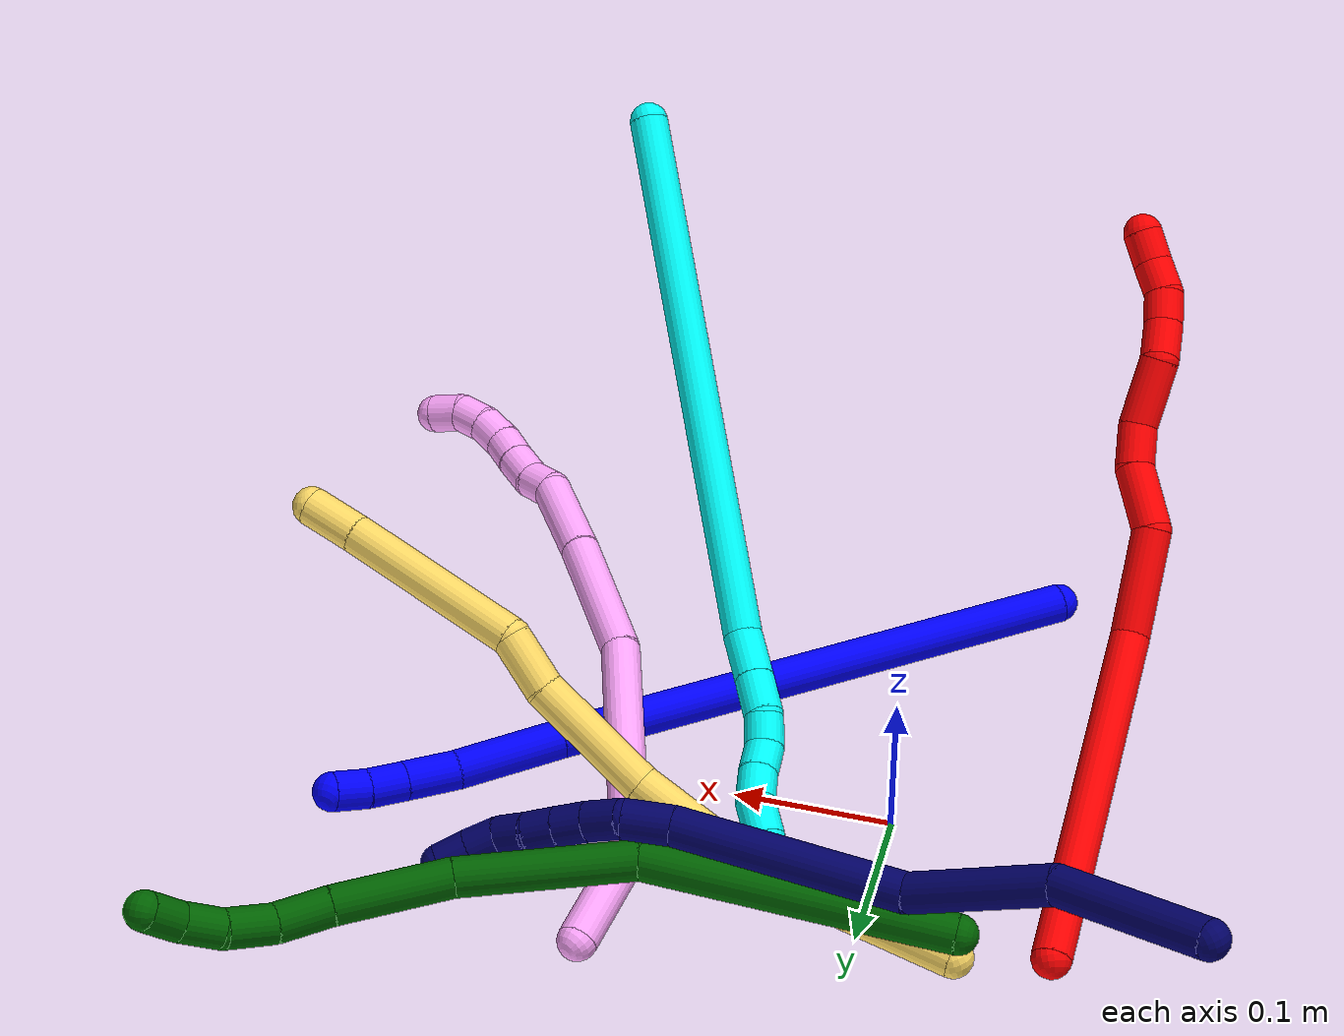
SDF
<sdf version="1.7">
 <world name="default">
  <plugin name="TubeGeneratorPlugin" filename="libtube_generator_plugin.so"/>
  <model name="photoneo_s_sensor">
   <static>1</static>
   <pose>0 0 2 1.57079 1.57079 3.14159</pose>
   <link name="link">
    <inertial><mass>0.1</mass></inertial>
    <sensor name="sensor" type="depth">
     <update_rate>30</update_rate>
     <camera>
      <horizontal_fov>1.22</horizontal_fov>
      <image><width>1920</width><height>1200</height><format>B8G8R8</format></image>
      <clip><near>0.1</near><far>4</far></clip>
      <depth_camera><output>points</output></depth_camera>
     </camera>
     <plugin name="camera_plugin" filename="libgazebo_ros_depth_camera.so">
      <baseline>0.2</baseline>
      <alwaysOn>1</alwaysOn>
      <updateRate>0.0</updateRate>
      <cameraName>camera_ir</cameraName>
      <imageTopicName>/camera/color/image_raw</imageTopicName>
      <cameraInfoTopicName>/camera/color/camera_info</cameraInfoTopicName>
      <depthImageTopicName>/camera/depth/image_raw</depthImageTopicName>
      <depthImageCameraInfoTopicName>/camera/depth/camera_info</depthImageCameraInfoTopicName>
      <pointCloudTopicName>/camera/depth/points</pointCloudTopicName>
      <frameName>fr_optical</frameName>
      <pointCloudCutoff>0.1</pointCloudCutoff>
      <pointCloudCutoffMax>2.0</pointCloudCutoffMax>
      <distortionK1>0</distortionK1>
      <distortionK2>0</distortionK2>
      <distortionK3>0</distortionK3>
      <distortionT1>0</distortionT1>
      <distortionT2>0</distortionT2>
      <CxPrime>0</CxPrime>
      <Cx>0</Cx>
      <Cy>0</Cy>
      <focalLength>0</focalLength>
      <hackBaseline>0</hackBaseline>
     </plugin>
    </sensor>
   </link>
  </model>
  <gravity>0 0 -9.8</gravity>
  <magnetic_field>6e-06 2.3e-05 -4.2e-05</magnetic_field>
  <atmosphere type="adiabatic"/>
  <physics name="default_physics" default="0" type="ode">
   <max_step_size>0.003</max_step_size>
   <real_time_factor>1</real_time_factor>
   <real_time_update_rate>1000</real_time_update_rate>
   <max_contacts>10000</max_contacts>
   <ode>
    <solver>
     <type>quick</type>
     <iters>100</iters>
     <sor>1.3</sor>
     <use_dynamic_moi_rescaling>0</use_dynamic_moi_rescaling>
    </solver>
    <constraints>
     <contact_max_correcting_vel>0</contact_max_correcting_vel>
     <contact_surface_layer>0.001</contact_surface_layer>
     <cfm>0</cfm>
     <erp>0.2</erp>
    </constraints>
   </ode>
  </physics>
  <scene><ambient>0.4 0.4 0.4 1</ambient><background>0.7 0.7 0.7 1</background><shadows>0</shadows></scene>
  <audio><device>default</device></audio>
  <spherical_coordinates>
   <surface_model>EARTH_WGS84</surface_model>
   <latitude_deg>0</latitude_deg>
   <longitude_deg>0</longitude_deg>
   <elevation>0</elevation>
   <heading_deg>0</heading_deg>
  </spherical_coordinates>
  <model name="bin">
   <static>1</static>
   <link name="bottom">
    <collision name="collision-bottom">
     <pose>0 0 -0.01 0 -0 0</pose>
     <geometry><box><size>0.8 0.6 0.02</size></box></geometry>
     <surface>
      <friction><ode><mu>100</mu><mu2>100</mu2></ode></friction>
      <contact><collide_bitmask>65535</collide_bitmask></contact>
     </surface>
    </collision>
   </link>
   <link name="west_wall">
    <collision name="collision-west_wall">
     <pose>-0.41 0 0.1 0 -0 0</pose>
     <geometry><box><size>0.02 0.6 0.2</size></box></geometry>
     <surface>
      <friction><ode><mu>100</mu><mu2>100</mu2></ode></friction>
      <contact><collide_bitmask>65535</collide_bitmask></contact>
     </surface>
    </collision>
   </link>
   <link name="east_wall">
    <collision name="collision-east_wall">
     <pose>0.41 0 0.1 0 -0 0</pose>
     <geometry><box><size>0.02 0.6 0.2</size></box></geometry>
     <surface>
      <friction><ode><mu>100</mu><mu2>100</mu2></ode></friction>
      <contact><collide_bitmask>65535</collide_bitmask></contact>
     </surface>
    </collision>
   </link>
   <link name="south_wall">
    <collision name="collision-south_wall">
     <pose>0 -0.31 0.1 0 -0 0</pose>
     <geometry><box><size>0.8 0.02 0.2</size></box></geometry>
     <surface>
      <friction><ode><mu>100</mu><mu2>100</mu2></ode></friction>
      <contact><collide_bitmask>65535</collide_bitmask></contact>
     </surface>
    </collision>
   </link>
   <link name="north_wall">
    <collision name="collision-north_wall">
     <pose>0 0.31 0.1 0 -0 0</pose>
     <geometry><box><size>0.8 0.02 0.2</size></box></geometry>
     <surface>
      <friction><ode><mu>100</mu><mu2>100</mu2></ode></friction>
      <contact><collide_bitmask>65535</collide_bitmask></contact>
     </surface>
    </collision>
   </link>
  </model>
  <model name="1">
   <static>0</static>
   <link name="1">
    <collision name="collision-cylinder-e_1_1_4">
     <pose>0.09911 0.076376 -0.121747 -2.58132 0.603713 -1.64977</pose>
     <geometry><cylinder><radius>0.0125</radius><length>0.349161</length></cylinder></geometry>
     <surface>
      <friction><ode><mu>1.16</mu><mu2>1.16</mu2><slip1>0</slip1><slip2>0</slip2></ode></friction>
      <contact><ode><kp>1e+06</kp><kd>1</kd><max_vel>0</max_vel><min_depth>0.001</min_depth></ode></contact>
     </surface>
    </collision>
    <visual name="visual-cylinder-e_1_1_4">
     <pose>0.09911 0.076376 -0.121747 -2.58132 0.603713 -1.64977</pose>
     <geometry><cylinder><radius>0.0125</radius><length>0.349161</length></cylinder></geometry>
     <material><ambient>0 0 1 1</ambient></material>
    </visual>
    <collision name="collision-cylinder-e_2_4_5">
     <pose>0.218502 0.166941 -0.267782 -2.61286 0.624704 -1.74627</pose>
     <geometry><cylinder><radius>0.0125</radius><length>0.069359</length></cylinder></geometry>
     <surface>
      <friction><ode><mu>1.16</mu><mu2>1.16</mu2><slip1>0</slip1><slip2>0</slip2></ode></friction>
      <contact><ode><kp>1e+06</kp><kd>1</kd><max_vel>0</max_vel><min_depth>0.001</min_depth></ode></contact>
     </surface>
    </collision>
    <visual name="visual-cylinder-e_2_4_5">
     <pose>0.218502 0.166941 -0.267782 -2.61286 0.624704 -1.74627</pose>
     <geometry><cylinder><radius>0.0125</radius><length>0.069359</length></cylinder></geometry>
     <material><ambient>0 0 1 1</ambient></material>
    </visual>
    <collision name="collision-cylinder-e_3_5_6">
     <pose>0.247347 0.190273 -0.304357 -2.50189 0.509792 -1.33311</pose>
     <geometry><cylinder><radius>0.0125</radius><length>0.03509</length></cylinder></geometry>
     <surface>
      <friction><ode><mu>1.16</mu><mu2>1.16</mu2><slip1>0</slip1><slip2>0</slip2></ode></friction>
      <contact><ode><kp>1e+06</kp><kd>1</kd><max_vel>0</max_vel><min_depth>0.001</min_depth></ode></contact>
     </surface>
    </collision>
    <visual name="visual-cylinder-e_3_5_6">
     <pose>0.247347 0.190273 -0.304357 -2.50189 0.509792 -1.33311</pose>
     <geometry><cylinder><radius>0.0125</radius><length>0.03509</length></cylinder></geometry>
     <material><ambient>0 0 1 1</ambient></material>
    </visual>
    <collision name="collision-cylinder-e_4_6_7">
     <pose>0.261772 0.20578 -0.325011 -2.49138 0.508727 -1.31405</pose>
     <geometry><cylinder><radius>0.0125</radius><length>0.024076</length></cylinder></geometry>
     <surface>
      <friction><ode><mu>1.16</mu><mu2>1.16</mu2><slip1>0</slip1><slip2>0</slip2></ode></friction>
      <contact><ode><kp>1e+06</kp><kd>1</kd><max_vel>0</max_vel><min_depth>0.001</min_depth></ode></contact>
     </surface>
    </collision>
    <visual name="visual-cylinder-e_4_6_7">
     <pose>0.261772 0.20578 -0.325011 -2.49138 0.508727 -1.31405</pose>
     <geometry><cylinder><radius>0.0125</radius><length>0.024076</length></cylinder></geometry>
     <material><ambient>0 0 1 1</ambient></material>
    </visual>
    <collision name="collision-cylinder-e_5_7_2">
     <pose>0.272993 0.219006 -0.340358 -2.36462 0.500923 -1.1173</pose>
     <geometry><cylinder><radius>0.0125</radius><length>0.022314</length></cylinder></geometry>
     <surface>
      <friction><ode><mu>1.16</mu><mu2>1.16</mu2><slip1>0</slip1><slip2>0</slip2></ode></friction>
      <contact><ode><kp>1e+06</kp><kd>1</kd><max_vel>0</max_vel><min_depth>0.001</min_depth></ode></contact>
     </surface>
    </collision>
    <visual name="visual-cylinder-e_5_7_2">
     <pose>0.272993 0.219006 -0.340358 -2.36462 0.500923 -1.1173</pose>
     <geometry><cylinder><radius>0.0125</radius><length>0.022314</length></cylinder></geometry>
     <material><ambient>0 0 1 1</ambient></material>
    </visual>
    <collision name="collision-sphere-2">
     <pose>0.278351 0.225867 -0.347336 0 -0 0</pose>
     <geometry><sphere><radius>0.0125</radius></sphere></geometry>
     <surface>
      <friction><ode><mu>1.16</mu><mu2>1.16</mu2><slip1>0</slip1><slip2>0</slip2></ode></friction>
      <contact><ode><kp>1e+06</kp><kd>1</kd><max_vel>0</max_vel><min_depth>0.001</min_depth></ode></contact>
     </surface>
    </collision>
    <visual name="visual-sphere-2">
     <pose>0.278351 0.225867 -0.347336 0 -0 0</pose>
     <geometry><sphere><radius>0.0125</radius></sphere></geometry>
     <material><ambient>0 0 1 1</ambient></material>
    </visual>
    <collision name="collision-sphere-7">
     <pose>0.267635 0.212144 -0.33338 0 -0 0</pose>
     <geometry><sphere><radius>0.0125</radius></sphere></geometry>
     <surface>
      <friction><ode><mu>1.16</mu><mu2>1.16</mu2><slip1>0</slip1><slip2>0</slip2></ode></friction>
      <contact><ode><kp>1e+06</kp><kd>1</kd><max_vel>0</max_vel><min_depth>0.001</min_depth></ode></contact>
     </surface>
    </collision>
    <visual name="visual-sphere-7">
     <pose>0.267635 0.212144 -0.33338 0 -0 0</pose>
     <geometry><sphere><radius>0.0125</radius></sphere></geometry>
     <material><ambient>0 0 1 1</ambient></material>
    </visual>
    <collision name="collision-sphere-6">
     <pose>0.255909 0.199415 -0.316643 0 -0 0</pose>
     <geometry><sphere><radius>0.0125</radius></sphere></geometry>
     <surface>
      <friction><ode><mu>1.16</mu><mu2>1.16</mu2><slip1>0</slip1><slip2>0</slip2></ode></friction>
      <contact><ode><kp>1e+06</kp><kd>1</kd><max_vel>0</max_vel><min_depth>0.001</min_depth></ode></contact>
     </surface>
    </collision>
    <visual name="visual-sphere-6">
     <pose>0.255909 0.199415 -0.316643 0 -0 0</pose>
     <geometry><sphere><radius>0.0125</radius></sphere></geometry>
     <material><ambient>0 0 1 1</ambient></material>
    </visual>
    <collision name="collision-sphere-5">
     <pose>0.238785 0.181131 -0.292071 0 -0 0</pose>
     <geometry><sphere><radius>0.0125</radius></sphere></geometry>
     <surface>
      <friction><ode><mu>1.16</mu><mu2>1.16</mu2><slip1>0</slip1><slip2>0</slip2></ode></friction>
      <contact><ode><kp>1e+06</kp><kd>1</kd><max_vel>0</max_vel><min_depth>0.001</min_depth></ode></contact>
     </surface>
    </collision>
    <visual name="visual-sphere-5">
     <pose>0.238785 0.181131 -0.292071 0 -0 0</pose>
     <geometry><sphere><radius>0.0125</radius></sphere></geometry>
     <material><ambient>0 0 1 1</ambient></material>
    </visual>
    <collision name="collision-sphere-1">
     <geometry><sphere><radius>0.0125</radius></sphere></geometry>
     <surface>
      <friction><ode><mu>1.16</mu><mu2>1.16</mu2><slip1>0</slip1><slip2>0</slip2></ode></friction>
      <contact><ode><kp>1e+06</kp><kd>1</kd><max_vel>0</max_vel><min_depth>0.001</min_depth></ode></contact>
     </surface>
    </collision>
    <visual name="visual-sphere-1">
     <geometry><sphere><radius>0.0125</radius></sphere></geometry>
     <material><ambient>0 0 1 1</ambient></material>
    </visual>
    <collision name="collision-sphere-4">
     <pose>0.19822 0.152752 -0.243494 0 -0 0</pose>
     <geometry><sphere><radius>0.0125</radius></sphere></geometry>
     <surface>
      <friction><ode><mu>1.16</mu><mu2>1.16</mu2><slip1>0</slip1><slip2>0</slip2></ode></friction>
      <contact><ode><kp>1e+06</kp><kd>1</kd><max_vel>0</max_vel><min_depth>0.001</min_depth></ode></contact>
     </surface>
    </collision>
    <visual name="visual-sphere-4">
     <pose>0.19822 0.152752 -0.243494 0 -0 0</pose>
     <geometry><sphere><radius>0.0125</radius></sphere></geometry>
     <material><ambient>0 0 1 1</ambient></material>
    </visual>
    <inertial>
     <pose>0.141668 0.109529 -0.174364 0 -0 0</pose>
     <mass>0.5</mass>
     <inertia>
      <ixx>-0.003166</ixx>
      <ixy>0</ixy>
      <ixz>0</ixz>
      <iyy>-0.001613</iyy>
      <iyz>0</iyz>
      <izz>-0.003646</izz>
     </inertia>
    </inertial>
   </link>
   <pose>-0.063598 -0.216545 0.011498 1.40872 0.50381 -0.214492</pose>
  </model>
  <model name="2">
   <static>0</static>
   <link name="2">
    <collision name="collision-cylinder-e_1_1_4">
     <pose>0.012173 -0.04728 0.103628 0.428035 0.106469 0.023162</pose>
     <geometry><cylinder><radius>0.0125</radius><length>0.229106</length></cylinder></geometry>
     <surface>
      <friction><ode><mu>1.16</mu><mu2>1.16</mu2><slip1>0</slip1><slip2>0</slip2></ode></friction>
      <contact><ode><kp>1e+06</kp><kd>1</kd><max_vel>0</max_vel><min_depth>0.001</min_depth></ode></contact>
     </surface>
    </collision>
    <visual name="visual-cylinder-e_1_1_4">
     <pose>0.012173 -0.04728 0.103628 0.428035 0.106469 0.023162</pose>
     <geometry><cylinder><radius>0.0125</radius><length>0.229106</length></cylinder></geometry>
     <material><ambient>1 0 0 1</ambient></material>
    </visual>
    <collision name="collision-cylinder-e_2_4_5">
     <pose>0.013866 -0.101926 0.239046 0.227712 -0.310753 -0.03582</pose>
     <geometry><cylinder><radius>0.0125</radius><length>0.068549</length></cylinder></geometry>
     <surface>
      <friction><ode><mu>1.16</mu><mu2>1.16</mu2><slip1>0</slip1><slip2>0</slip2></ode></friction>
      <contact><ode><kp>1e+06</kp><kd>1</kd><max_vel>0</max_vel><min_depth>0.001</min_depth></ode></contact>
     </surface>
    </collision>
    <visual name="visual-cylinder-e_2_4_5">
     <pose>0.013866 -0.101926 0.239046 0.227712 -0.310753 -0.03582</pose>
     <geometry><cylinder><radius>0.0125</radius><length>0.068549</length></cylinder></geometry>
     <material><ambient>1 0 0 1</ambient></material>
    </visual>
    <collision name="collision-cylinder-e_3_5_6">
     <pose>0.004775 -0.107198 0.292018 -0.09859 0.065142 -0.003215</pose>
     <geometry><cylinder><radius>0.0125</radius><length>0.04266</length></cylinder></geometry>
     <surface>
      <friction><ode><mu>1.16</mu><mu2>1.16</mu2><slip1>0</slip1><slip2>0</slip2></ode></friction>
      <contact><ode><kp>1e+06</kp><kd>1</kd><max_vel>0</max_vel><min_depth>0.001</min_depth></ode></contact>
     </surface>
    </collision>
    <visual name="visual-cylinder-e_3_5_6">
     <pose>0.004775 -0.107198 0.292018 -0.09859 0.065142 -0.003215</pose>
     <geometry><cylinder><radius>0.0125</radius><length>0.04266</length></cylinder></geometry>
     <material><ambient>1 0 0 1</ambient></material>
    </visual>
    <collision name="collision-cylinder-e_4_6_7">
     <pose>0.004498 -0.107509 0.326738 0.175894 -0.12048 -0.010636</pose>
     <geometry><cylinder><radius>0.0125</radius><length>0.027703</length></cylinder></geometry>
     <surface>
      <friction><ode><mu>1.16</mu><mu2>1.16</mu2><slip1>0</slip1><slip2>0</slip2></ode></friction>
      <contact><ode><kp>1e+06</kp><kd>1</kd><max_vel>0</max_vel><min_depth>0.001</min_depth></ode></contact>
     </surface>
    </collision>
    <visual name="visual-cylinder-e_4_6_7">
     <pose>0.004498 -0.107509 0.326738 0.175894 -0.12048 -0.010636</pose>
     <geometry><cylinder><radius>0.0125</radius><length>0.027703</length></cylinder></geometry>
     <material><ambient>1 0 0 1</ambient></material>
    </visual>
    <collision name="collision-cylinder-e_5_7_8">
     <pose>-0.007435 -0.115271 0.358763 0.281979 -0.490114 -0.070959</pose>
     <geometry><cylinder><radius>0.0125</radius><length>0.043627</length></cylinder></geometry>
     <surface>
      <friction><ode><mu>1.16</mu><mu2>1.16</mu2><slip1>0</slip1><slip2>0</slip2></ode></friction>
      <contact><ode><kp>1e+06</kp><kd>1</kd><max_vel>0</max_vel><min_depth>0.001</min_depth></ode></contact>
     </surface>
    </collision>
    <visual name="visual-cylinder-e_5_7_8">
     <pose>-0.007435 -0.115271 0.358763 0.281979 -0.490114 -0.070959</pose>
     <geometry><cylinder><radius>0.0125</radius><length>0.043627</length></cylinder></geometry>
     <material><ambient>1 0 0 1</ambient></material>
    </visual>
    <collision name="collision-cylinder-e_6_8_9">
     <pose>-0.017743 -0.123841 0.3893 0.260683 -0.003267 -0.000428</pose>
     <geometry><cylinder><radius>0.0125</radius><length>0.024947</length></cylinder></geometry>
     <surface>
      <friction><ode><mu>1.16</mu><mu2>1.16</mu2><slip1>0</slip1><slip2>0</slip2></ode></friction>
      <contact><ode><kp>1e+06</kp><kd>1</kd><max_vel>0</max_vel><min_depth>0.001</min_depth></ode></contact>
     </surface>
    </collision>
    <visual name="visual-cylinder-e_6_8_9">
     <pose>-0.017743 -0.123841 0.3893 0.260683 -0.003267 -0.000428</pose>
     <geometry><cylinder><radius>0.0125</radius><length>0.024947</length></cylinder></geometry>
     <material><ambient>1 0 0 1</ambient></material>
    </visual>
    <collision name="collision-cylinder-e_7_9_10">
     <pose>-0.018654 -0.128423 0.411747 0.130775 -0.082748 -0.005421</pose>
     <geometry><cylinder><radius>0.0125</radius><length>0.021041</length></cylinder></geometry>
     <surface>
      <friction><ode><mu>1.16</mu><mu2>1.16</mu2><slip1>0</slip1><slip2>0</slip2></ode></friction>
      <contact><ode><kp>1e+06</kp><kd>1</kd><max_vel>0</max_vel><min_depth>0.001</min_depth></ode></contact>
     </surface>
    </collision>
    <visual name="visual-cylinder-e_7_9_10">
     <pose>-0.018654 -0.128423 0.411747 0.130775 -0.082748 -0.005421</pose>
     <geometry><cylinder><radius>0.0125</radius><length>0.021041</length></cylinder></geometry>
     <material><ambient>1 0 0 1</ambient></material>
    </visual>
    <collision name="collision-cylinder-e_8_10_11">
     <pose>-0.018627 -0.12796 0.432793 -0.170133 0.082732 -0.007059</pose>
     <geometry><cylinder><radius>0.0125</radius><length>0.021688</length></cylinder></geometry>
     <surface>
      <friction><ode><mu>1.16</mu><mu2>1.16</mu2><slip1>0</slip1><slip2>0</slip2></ode></friction>
      <contact><ode><kp>1e+06</kp><kd>1</kd><max_vel>0</max_vel><min_depth>0.001</min_depth></ode></contact>
     </surface>
    </collision>
    <visual name="visual-cylinder-e_8_10_11">
     <pose>-0.018627 -0.12796 0.432793 -0.170133 0.082732 -0.007059</pose>
     <geometry><cylinder><radius>0.0125</radius><length>0.021688</length></cylinder></geometry>
     <material><ambient>1 0 0 1</ambient></material>
    </visual>
    <collision name="collision-cylinder-e_9_11_2">
     <pose>-0.018688 -0.123643 0.453434 -0.244047 -0.092658 0.011371</pose>
     <geometry><cylinder><radius>0.0125</radius><length>0.02068</length></cylinder></geometry>
     <surface>
      <friction><ode><mu>1.16</mu><mu2>1.16</mu2><slip1>0</slip1><slip2>0</slip2></ode></friction>
      <contact><ode><kp>1e+06</kp><kd>1</kd><max_vel>0</max_vel><min_depth>0.001</min_depth></ode></contact>
     </surface>
    </collision>
    <visual name="visual-cylinder-e_9_11_2">
     <pose>-0.018688 -0.123643 0.453434 -0.244047 -0.092658 0.011371</pose>
     <geometry><cylinder><radius>0.0125</radius><length>0.02068</length></cylinder></geometry>
     <material><ambient>1 0 0 1</ambient></material>
    </visual>
    <collision name="collision-sphere-2">
     <pose>-0.019644 -0.121155 0.463425 0 -0 0</pose>
     <geometry><sphere><radius>0.0125</radius></sphere></geometry>
     <surface>
      <friction><ode><mu>1.16</mu><mu2>1.16</mu2><slip1>0</slip1><slip2>0</slip2></ode></friction>
      <contact><ode><kp>1e+06</kp><kd>1</kd><max_vel>0</max_vel><min_depth>0.001</min_depth></ode></contact>
     </surface>
    </collision>
    <visual name="visual-sphere-2">
     <pose>-0.019644 -0.121155 0.463425 0 -0 0</pose>
     <geometry><sphere><radius>0.0125</radius></sphere></geometry>
     <material><ambient>1 0 0 1</ambient></material>
    </visual>
    <collision name="collision-sphere-11">
     <pose>-0.017731 -0.126131 0.443444 0 -0 0</pose>
     <geometry><sphere><radius>0.0125</radius></sphere></geometry>
     <surface>
      <friction><ode><mu>1.16</mu><mu2>1.16</mu2><slip1>0</slip1><slip2>0</slip2></ode></friction>
      <contact><ode><kp>1e+06</kp><kd>1</kd><max_vel>0</max_vel><min_depth>0.001</min_depth></ode></contact>
     </surface>
    </collision>
    <visual name="visual-sphere-11">
     <pose>-0.017731 -0.126131 0.443444 0 -0 0</pose>
     <geometry><sphere><radius>0.0125</radius></sphere></geometry>
     <material><ambient>1 0 0 1</ambient></material>
    </visual>
    <collision name="collision-sphere-10">
     <pose>-0.019523 -0.12979 0.422141 0 -0 0</pose>
     <geometry><sphere><radius>0.0125</radius></sphere></geometry>
     <surface>
      <friction><ode><mu>1.16</mu><mu2>1.16</mu2><slip1>0</slip1><slip2>0</slip2></ode></friction>
      <contact><ode><kp>1e+06</kp><kd>1</kd><max_vel>0</max_vel><min_depth>0.001</min_depth></ode></contact>
     </surface>
    </collision>
    <visual name="visual-sphere-10">
     <pose>-0.019523 -0.12979 0.422141 0 -0 0</pose>
     <geometry><sphere><radius>0.0125</radius></sphere></geometry>
     <material><ambient>1 0 0 1</ambient></material>
    </visual>
    <collision name="collision-sphere-9">
     <pose>-0.017784 -0.127056 0.401352 0 -0 0</pose>
     <geometry><sphere><radius>0.0125</radius></sphere></geometry>
     <surface>
      <friction><ode><mu>1.16</mu><mu2>1.16</mu2><slip1>0</slip1><slip2>0</slip2></ode></friction>
      <contact><ode><kp>1e+06</kp><kd>1</kd><max_vel>0</max_vel><min_depth>0.001</min_depth></ode></contact>
     </surface>
    </collision>
    <visual name="visual-sphere-9">
     <pose>-0.017784 -0.127056 0.401352 0 -0 0</pose>
     <geometry><sphere><radius>0.0125</radius></sphere></geometry>
     <material><ambient>1 0 0 1</ambient></material>
    </visual>
    <collision name="collision-sphere-4">
     <pose>0.024347 -0.09456 0.207256 0 -0 0</pose>
     <geometry><sphere><radius>0.0125</radius></sphere></geometry>
     <surface>
      <friction><ode><mu>1.16</mu><mu2>1.16</mu2><slip1>0</slip1><slip2>0</slip2></ode></friction>
      <contact><ode><kp>1e+06</kp><kd>1</kd><max_vel>0</max_vel><min_depth>0.001</min_depth></ode></contact>
     </surface>
    </collision>
    <visual name="visual-sphere-4">
     <pose>0.024347 -0.09456 0.207256 0 -0 0</pose>
     <geometry><sphere><radius>0.0125</radius></sphere></geometry>
     <material><ambient>1 0 0 1</ambient></material>
    </visual>
    <collision name="collision-sphere-1">
     <geometry><sphere><radius>0.0125</radius></sphere></geometry>
     <surface>
      <friction><ode><mu>1.16</mu><mu2>1.16</mu2><slip1>0</slip1><slip2>0</slip2></ode></friction>
      <contact><ode><kp>1e+06</kp><kd>1</kd><max_vel>0</max_vel><min_depth>0.001</min_depth></ode></contact>
     </surface>
    </collision>
    <visual name="visual-sphere-1">
     <geometry><sphere><radius>0.0125</radius></sphere></geometry>
     <material><ambient>1 0 0 1</ambient></material>
    </visual>
    <collision name="collision-sphere-8">
     <pose>-0.017703 -0.120626 0.377248 0 -0 0</pose>
     <geometry><sphere><radius>0.0125</radius></sphere></geometry>
     <surface>
      <friction><ode><mu>1.16</mu><mu2>1.16</mu2><slip1>0</slip1><slip2>0</slip2></ode></friction>
      <contact><ode><kp>1e+06</kp><kd>1</kd><max_vel>0</max_vel><min_depth>0.001</min_depth></ode></contact>
     </surface>
    </collision>
    <visual name="visual-sphere-8">
     <pose>-0.017703 -0.120626 0.377248 0 -0 0</pose>
     <geometry><sphere><radius>0.0125</radius></sphere></geometry>
     <material><ambient>1 0 0 1</ambient></material>
    </visual>
    <collision name="collision-sphere-5">
     <pose>0.003386 -0.109293 0.270837 0 -0 0</pose>
     <geometry><sphere><radius>0.0125</radius></sphere></geometry>
     <surface>
      <friction><ode><mu>1.16</mu><mu2>1.16</mu2><slip1>0</slip1><slip2>0</slip2></ode></friction>
      <contact><ode><kp>1e+06</kp><kd>1</kd><max_vel>0</max_vel><min_depth>0.001</min_depth></ode></contact>
     </surface>
    </collision>
    <visual name="visual-sphere-5">
     <pose>0.003386 -0.109293 0.270837 0 -0 0</pose>
     <geometry><sphere><radius>0.0125</radius></sphere></geometry>
     <material><ambient>1 0 0 1</ambient></material>
    </visual>
    <collision name="collision-sphere-6">
     <pose>0.006163 -0.105103 0.313199 0 -0 0</pose>
     <geometry><sphere><radius>0.0125</radius></sphere></geometry>
     <surface>
      <friction><ode><mu>1.16</mu><mu2>1.16</mu2><slip1>0</slip1><slip2>0</slip2></ode></friction>
      <contact><ode><kp>1e+06</kp><kd>1</kd><max_vel>0</max_vel><min_depth>0.001</min_depth></ode></contact>
     </surface>
    </collision>
    <visual name="visual-sphere-6">
     <pose>0.006163 -0.105103 0.313199 0 -0 0</pose>
     <geometry><sphere><radius>0.0125</radius></sphere></geometry>
     <material><ambient>1 0 0 1</ambient></material>
    </visual>
    <collision name="collision-sphere-7">
     <pose>0.002833 -0.109916 0.340277 0 -0 0</pose>
     <geometry><sphere><radius>0.0125</radius></sphere></geometry>
     <surface>
      <friction><ode><mu>1.16</mu><mu2>1.16</mu2><slip1>0</slip1><slip2>0</slip2></ode></friction>
      <contact><ode><kp>1e+06</kp><kd>1</kd><max_vel>0</max_vel><min_depth>0.001</min_depth></ode></contact>
     </surface>
    </collision>
    <visual name="visual-sphere-7">
     <pose>0.002833 -0.109916 0.340277 0 -0 0</pose>
     <geometry><sphere><radius>0.0125</radius></sphere></geometry>
     <material><ambient>1 0 0 1</ambient></material>
    </visual>
    <inertial>
     <pose>0.004236 -0.083046 0.228856 0 -0 0</pose>
     <mass>0.5</mass>
     <inertia>
      <ixx>0.001079</ixx>
      <ixy>0</ixy>
      <ixz>0</ixz>
      <iyy>0.000988</iyy>
      <iyz>0</iyz>
      <izz>0.000367</izz>
     </inertia>
    </inertial>
   </link>
   <pose>-0.117789 0.094659 0.011494 0.4271 0.972973 -0.6906</pose>
  </model>
  <model name="3">
   <static>0</static>
   <link name="3">
    <collision name="collision-cylinder-e_1_1_4">
     <pose>0.017234 0.011974 -0.174847 -3.07322 0.098021 -1.92383</pose>
     <geometry><cylinder><radius>0.0125</radius><length>0.352204</length></cylinder></geometry>
     <surface>
      <friction><ode><mu>1.16</mu><mu2>1.16</mu2><slip1>0</slip1><slip2>0</slip2></ode></friction>
      <contact><ode><kp>1e+06</kp><kd>1</kd><max_vel>0</max_vel><min_depth>0.001</min_depth></ode></contact>
     </surface>
    </collision>
    <visual name="visual-cylinder-e_1_1_4">
     <pose>0.017234 0.011974 -0.174847 -3.07322 0.098021 -1.92383</pose>
     <geometry><cylinder><radius>0.0125</radius><length>0.352204</length></cylinder></geometry>
     <material><ambient>0.003922 1 0.996078 1</ambient></material>
    </visual>
    <collision name="collision-cylinder-e_2_4_5">
     <pose>0.031324 0.027461 -0.365393 -2.92138 -0.193033 1.43853</pose>
     <geometry><cylinder><radius>0.0125</radius><length>0.032783</length></cylinder></geometry>
     <surface>
      <friction><ode><mu>1.16</mu><mu2>1.16</mu2><slip1>0</slip1><slip2>0</slip2></ode></friction>
      <contact><ode><kp>1e+06</kp><kd>1</kd><max_vel>0</max_vel><min_depth>0.001</min_depth></ode></contact>
     </surface>
    </collision>
    <visual name="visual-cylinder-e_2_4_5">
     <pose>0.031324 0.027461 -0.365393 -2.92138 -0.193033 1.43853</pose>
     <geometry><cylinder><radius>0.0125</radius><length>0.032783</length></cylinder></geometry>
     <material><ambient>0.003922 1 0.996078 1</ambient></material>
    </visual>
    <collision name="collision-cylinder-e_3_5_6">
     <pose>0.025849 0.033903 -0.394123 -2.92063 -0.1727 1.32529</pose>
     <geometry><cylinder><radius>0.0125</radius><length>0.027117</length></cylinder></geometry>
     <surface>
      <friction><ode><mu>1.16</mu><mu2>1.16</mu2><slip1>0</slip1><slip2>0</slip2></ode></friction>
      <contact><ode><kp>1e+06</kp><kd>1</kd><max_vel>0</max_vel><min_depth>0.001</min_depth></ode></contact>
     </surface>
    </collision>
    <visual name="visual-cylinder-e_3_5_6">
     <pose>0.025849 0.033903 -0.394123 -2.92063 -0.1727 1.32529</pose>
     <geometry><cylinder><radius>0.0125</radius><length>0.027117</length></cylinder></geometry>
     <material><ambient>0.003922 1 0.996078 1</ambient></material>
    </visual>
    <collision name="collision-cylinder-e_4_6_7">
     <pose>0.024867 0.039186 -0.416888 -2.90412 0.133741 -1.02306</pose>
     <geometry><cylinder><radius>0.0125</radius><length>0.020207</length></cylinder></geometry>
     <surface>
      <friction><ode><mu>1.16</mu><mu2>1.16</mu2><slip1>0</slip1><slip2>0</slip2></ode></friction>
      <contact><ode><kp>1e+06</kp><kd>1</kd><max_vel>0</max_vel><min_depth>0.001</min_depth></ode></contact>
     </surface>
    </collision>
    <visual name="visual-cylinder-e_4_6_7">
     <pose>0.024867 0.039186 -0.416888 -2.90412 0.133741 -1.02306</pose>
     <geometry><cylinder><radius>0.0125</radius><length>0.020207</length></cylinder></geometry>
     <material><ambient>0.003922 1 0.996078 1</ambient></material>
    </visual>
    <collision name="collision-cylinder-e_5_7_8">
     <pose>0.025944 0.047518 -0.434926 -2.51783 -0.026318 0.08159</pose>
     <geometry><cylinder><radius>0.0125</radius><length>0.020472</length></cylinder></geometry>
     <surface>
      <friction><ode><mu>1.16</mu><mu2>1.16</mu2><slip1>0</slip1><slip2>0</slip2></ode></friction>
      <contact><ode><kp>1e+06</kp><kd>1</kd><max_vel>0</max_vel><min_depth>0.001</min_depth></ode></contact>
     </surface>
    </collision>
    <visual name="visual-cylinder-e_5_7_8">
     <pose>0.025944 0.047518 -0.434926 -2.51783 -0.026318 0.08159</pose>
     <geometry><cylinder><radius>0.0125</radius><length>0.020472</length></cylinder></geometry>
     <material><ambient>0.003922 1 0.996078 1</ambient></material>
    </visual>
    <collision name="collision-cylinder-e_6_8_9">
     <pose>0.024586 0.058903 -0.452338 -2.60563 -0.102504 0.36937</pose>
     <geometry><cylinder><radius>0.0125</radius><length>0.021295</length></cylinder></geometry>
     <surface>
      <friction><ode><mu>1.16</mu><mu2>1.16</mu2><slip1>0</slip1><slip2>0</slip2></ode></friction>
      <contact><ode><kp>1e+06</kp><kd>1</kd><max_vel>0</max_vel><min_depth>0.001</min_depth></ode></contact>
     </surface>
    </collision>
    <visual name="visual-cylinder-e_6_8_9">
     <pose>0.024586 0.058903 -0.452338 -2.60563 -0.102504 0.36937</pose>
     <geometry><cylinder><radius>0.0125</radius><length>0.021295</length></cylinder></geometry>
     <material><ambient>0.003922 1 0.996078 1</ambient></material>
    </visual>
    <collision name="collision-cylinder-e_7_9_2">
     <pose>0.02145 0.066667 -0.474024 -2.95654 -0.158549 1.41607</pose>
     <geometry><cylinder><radius>0.0125</radius><length>0.025922</length></cylinder></geometry>
     <surface>
      <friction><ode><mu>1.16</mu><mu2>1.16</mu2><slip1>0</slip1><slip2>0</slip2></ode></friction>
      <contact><ode><kp>1e+06</kp><kd>1</kd><max_vel>0</max_vel><min_depth>0.001</min_depth></ode></contact>
     </surface>
    </collision>
    <visual name="visual-cylinder-e_7_9_2">
     <pose>0.02145 0.066667 -0.474024 -2.95654 -0.158549 1.41607</pose>
     <geometry><cylinder><radius>0.0125</radius><length>0.025922</length></cylinder></geometry>
     <material><ambient>0.003922 1 0.996078 1</ambient></material>
    </visual>
    <collision name="collision-sphere-2">
     <pose>0.019403 0.069022 -0.486604 0 -0 0</pose>
     <geometry><sphere><radius>0.0125</radius></sphere></geometry>
     <surface>
      <friction><ode><mu>1.16</mu><mu2>1.16</mu2><slip1>0</slip1><slip2>0</slip2></ode></friction>
      <contact><ode><kp>1e+06</kp><kd>1</kd><max_vel>0</max_vel><min_depth>0.001</min_depth></ode></contact>
     </surface>
    </collision>
    <visual name="visual-sphere-2">
     <pose>0.019403 0.069022 -0.486604 0 -0 0</pose>
     <geometry><sphere><radius>0.0125</radius></sphere></geometry>
     <material><ambient>0.003922 1 0.996078 1</ambient></material>
    </visual>
    <collision name="collision-sphere-9">
     <pose>0.023496 0.064312 -0.461444 0 -0 0</pose>
     <geometry><sphere><radius>0.0125</radius></sphere></geometry>
     <surface>
      <friction><ode><mu>1.16</mu><mu2>1.16</mu2><slip1>0</slip1><slip2>0</slip2></ode></friction>
      <contact><ode><kp>1e+06</kp><kd>1</kd><max_vel>0</max_vel><min_depth>0.001</min_depth></ode></contact>
     </surface>
    </collision>
    <visual name="visual-sphere-9">
     <pose>0.023496 0.064312 -0.461444 0 -0 0</pose>
     <geometry><sphere><radius>0.0125</radius></sphere></geometry>
     <material><ambient>0.003922 1 0.996078 1</ambient></material>
    </visual>
    <collision name="collision-sphere-4">
     <pose>0.034468 0.023947 -0.349695 0 -0 0</pose>
     <geometry><sphere><radius>0.0125</radius></sphere></geometry>
     <surface>
      <friction><ode><mu>1.16</mu><mu2>1.16</mu2><slip1>0</slip1><slip2>0</slip2></ode></friction>
      <contact><ode><kp>1e+06</kp><kd>1</kd><max_vel>0</max_vel><min_depth>0.001</min_depth></ode></contact>
     </surface>
    </collision>
    <visual name="visual-sphere-4">
     <pose>0.034468 0.023947 -0.349695 0 -0 0</pose>
     <geometry><sphere><radius>0.0125</radius></sphere></geometry>
     <material><ambient>0.003922 1 0.996078 1</ambient></material>
    </visual>
    <collision name="collision-sphere-1">
     <geometry><sphere><radius>0.0125</radius></sphere></geometry>
     <surface>
      <friction><ode><mu>1.16</mu><mu2>1.16</mu2><slip1>0</slip1><slip2>0</slip2></ode></friction>
      <contact><ode><kp>1e+06</kp><kd>1</kd><max_vel>0</max_vel><min_depth>0.001</min_depth></ode></contact>
     </surface>
    </collision>
    <visual name="visual-sphere-1">
     <geometry><sphere><radius>0.0125</radius></sphere></geometry>
     <material><ambient>0.003922 1 0.996078 1</ambient></material>
    </visual>
    <collision name="collision-sphere-8">
     <pose>0.025675 0.053494 -0.443231 0 -0 0</pose>
     <geometry><sphere><radius>0.0125</radius></sphere></geometry>
     <surface>
      <friction><ode><mu>1.16</mu><mu2>1.16</mu2><slip1>0</slip1><slip2>0</slip2></ode></friction>
      <contact><ode><kp>1e+06</kp><kd>1</kd><max_vel>0</max_vel><min_depth>0.001</min_depth></ode></contact>
     </surface>
    </collision>
    <visual name="visual-sphere-8">
     <pose>0.025675 0.053494 -0.443231 0 -0 0</pose>
     <geometry><sphere><radius>0.0125</radius></sphere></geometry>
     <material><ambient>0.003922 1 0.996078 1</ambient></material>
    </visual>
    <collision name="collision-sphere-5">
     <pose>0.028179 0.030975 -0.381091 0 -0 0</pose>
     <geometry><sphere><radius>0.0125</radius></sphere></geometry>
     <surface>
      <friction><ode><mu>1.16</mu><mu2>1.16</mu2><slip1>0</slip1><slip2>0</slip2></ode></friction>
      <contact><ode><kp>1e+06</kp><kd>1</kd><max_vel>0</max_vel><min_depth>0.001</min_depth></ode></contact>
     </surface>
    </collision>
    <visual name="visual-sphere-5">
     <pose>0.028179 0.030975 -0.381091 0 -0 0</pose>
     <geometry><sphere><radius>0.0125</radius></sphere></geometry>
     <material><ambient>0.003922 1 0.996078 1</ambient></material>
    </visual>
    <collision name="collision-sphere-6">
     <pose>0.023519 0.03683 -0.407156 0 -0 0</pose>
     <geometry><sphere><radius>0.0125</radius></sphere></geometry>
     <surface>
      <friction><ode><mu>1.16</mu><mu2>1.16</mu2><slip1>0</slip1><slip2>0</slip2></ode></friction>
      <contact><ode><kp>1e+06</kp><kd>1</kd><max_vel>0</max_vel><min_depth>0.001</min_depth></ode></contact>
     </surface>
    </collision>
    <visual name="visual-sphere-6">
     <pose>0.023519 0.03683 -0.407156 0 -0 0</pose>
     <geometry><sphere><radius>0.0125</radius></sphere></geometry>
     <material><ambient>0.003922 1 0.996078 1</ambient></material>
    </visual>
    <collision name="collision-sphere-7">
     <pose>0.026214 0.041541 -0.42662 0 -0 0</pose>
     <geometry><sphere><radius>0.0125</radius></sphere></geometry>
     <surface>
      <friction><ode><mu>1.16</mu><mu2>1.16</mu2><slip1>0</slip1><slip2>0</slip2></ode></friction>
      <contact><ode><kp>1e+06</kp><kd>1</kd><max_vel>0</max_vel><min_depth>0.001</min_depth></ode></contact>
     </surface>
    </collision>
    <visual name="visual-sphere-7">
     <pose>0.026214 0.041541 -0.42662 0 -0 0</pose>
     <geometry><sphere><radius>0.0125</radius></sphere></geometry>
     <material><ambient>0.003922 1 0.996078 1</ambient></material>
    </visual>
    <inertial>
     <pose>0.019822 0.021568 -0.246992 0 -0 0</pose>
     <mass>0.5</mass>
     <inertia>
      <ixx>-0.004655</ixx>
      <ixy>0</ixy>
      <ixz>0</ixz>
      <iyy>-0.00212</iyy>
      <iyz>0</iyz>
      <izz>-0.000646</izz>
     </inertia>
    </inertial>
   </link>
   <pose>0.250337 -0.346461 0.250673 0.635868 0.880218 -0.208793</pose>
  </model>
  <model name="4">
   <static>0</static>
   <link name="4">
    <collision name="collision-cylinder-e_1_1_4">
     <pose>0.005 -0.005109 -0.035358 2.99808 0.139044 1.5391</pose>
     <geometry><cylinder><radius>0.0125</radius><length>0.072147</length></cylinder></geometry>
     <surface>
      <friction><ode><mu>1.16</mu><mu2>1.16</mu2><slip1>0</slip1><slip2>0</slip2></ode></friction>
      <contact><ode><kp>1e+06</kp><kd>1</kd><max_vel>0</max_vel><min_depth>0.001</min_depth></ode></contact>
     </surface>
    </collision>
    <visual name="visual-cylinder-e_1_1_4">
     <pose>0.005 -0.005109 -0.035358 2.99808 0.139044 1.5391</pose>
     <geometry><cylinder><radius>0.0125</radius><length>0.072147</length></cylinder></geometry>
     <material><ambient>1 0.65098 0.996078 1</ambient></material>
    </visual>
    <collision name="collision-cylinder-e_2_4_5">
     <pose>0.048336 -0.04329 -0.132238 2.64835 0.501971 1.58908</pose>
     <geometry><cylinder><radius>0.0125</radius><length>0.159353</length></cylinder></geometry>
     <surface>
      <friction><ode><mu>1.16</mu><mu2>1.16</mu2><slip1>0</slip1><slip2>0</slip2></ode></friction>
      <contact><ode><kp>1e+06</kp><kd>1</kd><max_vel>0</max_vel><min_depth>0.001</min_depth></ode></contact>
     </surface>
    </collision>
    <visual name="visual-cylinder-e_2_4_5">
     <pose>0.048336 -0.04329 -0.132238 2.64835 0.501971 1.58908</pose>
     <geometry><cylinder><radius>0.0125</radius><length>0.159353</length></cylinder></geometry>
     <material><ambient>1 0.65098 0.996078 1</ambient></material>
    </visual>
    <collision name="collision-cylinder-e_3_5_6">
     <pose>0.111928 -0.101152 -0.218507 2.35535 0.624672 1.32315</pose>
     <geometry><cylinder><radius>0.0125</radius><length>0.086367</length></cylinder></geometry>
     <surface>
      <friction><ode><mu>1.16</mu><mu2>1.16</mu2><slip1>0</slip1><slip2>0</slip2></ode></friction>
      <contact><ode><kp>1e+06</kp><kd>1</kd><max_vel>0</max_vel><min_depth>0.001</min_depth></ode></contact>
     </surface>
    </collision>
    <visual name="visual-cylinder-e_3_5_6">
     <pose>0.111928 -0.101152 -0.218507 2.35535 0.624672 1.32315</pose>
     <geometry><cylinder><radius>0.0125</radius><length>0.086367</length></cylinder></geometry>
     <material><ambient>1 0.65098 0.996078 1</ambient></material>
    </visual>
    <collision name="collision-cylinder-e_4_6_7">
     <pose>0.15622 -0.141344 -0.259545 2.38419 0.704008 1.49084</pose>
     <geometry><cylinder><radius>0.0125</radius><length>0.058821</length></cylinder></geometry>
     <surface>
      <friction><ode><mu>1.16</mu><mu2>1.16</mu2><slip1>0</slip1><slip2>0</slip2></ode></friction>
      <contact><ode><kp>1e+06</kp><kd>1</kd><max_vel>0</max_vel><min_depth>0.001</min_depth></ode></contact>
     </surface>
    </collision>
    <visual name="visual-cylinder-e_4_6_7">
     <pose>0.15622 -0.141344 -0.259545 2.38419 0.704008 1.49084</pose>
     <geometry><cylinder><radius>0.0125</radius><length>0.058821</length></cylinder></geometry>
     <material><ambient>1 0.65098 0.996078 1</ambient></material>
    </visual>
    <collision name="collision-cylinder-e_5_7_8">
     <pose>0.183938 -0.161562 -0.277162 1.83981 1.04863 1.29888</pose>
     <geometry><cylinder><radius>0.0125</radius><length>0.020032</length></cylinder></geometry>
     <surface>
      <friction><ode><mu>1.16</mu><mu2>1.16</mu2><slip1>0</slip1><slip2>0</slip2></ode></friction>
      <contact><ode><kp>1e+06</kp><kd>1</kd><max_vel>0</max_vel><min_depth>0.001</min_depth></ode></contact>
     </surface>
    </collision>
    <visual name="visual-cylinder-e_5_7_8">
     <pose>0.183938 -0.161562 -0.277162 1.83981 1.04863 1.29888</pose>
     <geometry><cylinder><radius>0.0125</radius><length>0.020032</length></cylinder></geometry>
     <material><ambient>1 0.65098 0.996078 1</ambient></material>
    </visual>
    <collision name="collision-cylinder-e_6_8_9">
     <pose>0.200399 -0.172744 -0.282641 2.14859 0.797121 1.32145</pose>
     <geometry><cylinder><radius>0.0125</radius><length>0.021751</length></cylinder></geometry>
     <surface>
      <friction><ode><mu>1.16</mu><mu2>1.16</mu2><slip1>0</slip1><slip2>0</slip2></ode></friction>
      <contact><ode><kp>1e+06</kp><kd>1</kd><max_vel>0</max_vel><min_depth>0.001</min_depth></ode></contact>
     </surface>
    </collision>
    <visual name="visual-cylinder-e_6_8_9">
     <pose>0.200399 -0.172744 -0.282641 2.14859 0.797121 1.32145</pose>
     <geometry><cylinder><radius>0.0125</radius><length>0.021751</length></cylinder></geometry>
     <material><ambient>1 0.65098 0.996078 1</ambient></material>
    </visual>
    <collision name="collision-cylinder-e_7_9_10">
     <pose>0.215303 -0.184718 -0.291266 2.24425 0.781886 1.41609</pose>
     <geometry><cylinder><radius>0.0125</radius><length>0.020222</length></cylinder></geometry>
     <surface>
      <friction><ode><mu>1.16</mu><mu2>1.16</mu2><slip1>0</slip1><slip2>0</slip2></ode></friction>
      <contact><ode><kp>1e+06</kp><kd>1</kd><max_vel>0</max_vel><min_depth>0.001</min_depth></ode></contact>
     </surface>
    </collision>
    <visual name="visual-cylinder-e_7_9_10">
     <pose>0.215303 -0.184718 -0.291266 2.24425 0.781886 1.41609</pose>
     <geometry><cylinder><radius>0.0125</radius><length>0.020222</length></cylinder></geometry>
     <material><ambient>1 0.65098 0.996078 1</ambient></material>
    </visual>
    <collision name="collision-cylinder-e_8_10_11">
     <pose>0.229462 -0.197231 -0.298173 1.90952 0.765454 1.03411</pose>
     <geometry><cylinder><radius>0.0125</radius><length>0.020307</length></cylinder></geometry>
     <surface>
      <friction><ode><mu>1.16</mu><mu2>1.16</mu2><slip1>0</slip1><slip2>0</slip2></ode></friction>
      <contact><ode><kp>1e+06</kp><kd>1</kd><max_vel>0</max_vel><min_depth>0.001</min_depth></ode></contact>
     </surface>
    </collision>
    <visual name="visual-cylinder-e_8_10_11">
     <pose>0.229462 -0.197231 -0.298173 1.90952 0.765454 1.03411</pose>
     <geometry><cylinder><radius>0.0125</radius><length>0.020307</length></cylinder></geometry>
     <material><ambient>1 0.65098 0.996078 1</ambient></material>
    </visual>
    <collision name="collision-cylinder-e_9_11_12">
     <pose>0.244772 -0.210283 -0.301043 1.64169 0.930767 0.988871</pose>
     <geometry><cylinder><radius>0.0125</radius><length>0.020633</length></cylinder></geometry>
     <surface>
      <friction><ode><mu>1.16</mu><mu2>1.16</mu2><slip1>0</slip1><slip2>0</slip2></ode></friction>
      <contact><ode><kp>1e+06</kp><kd>1</kd><max_vel>0</max_vel><min_depth>0.001</min_depth></ode></contact>
     </surface>
    </collision>
    <visual name="visual-cylinder-e_9_11_12">
     <pose>0.244772 -0.210283 -0.301043 1.64169 0.930767 0.988871</pose>
     <geometry><cylinder><radius>0.0125</radius><length>0.020633</length></cylinder></geometry>
     <material><ambient>1 0.65098 0.996078 1</ambient></material>
    </visual>
    <collision name="collision-cylinder-e_10_12_2">
     <pose>0.261858 -0.22022 -0.298061 0.837228 1.0457 0.502035</pose>
     <geometry><cylinder><radius>0.0125</radius><length>0.020366</length></cylinder></geometry>
     <surface>
      <friction><ode><mu>1.16</mu><mu2>1.16</mu2><slip1>0</slip1><slip2>0</slip2></ode></friction>
      <contact><ode><kp>1e+06</kp><kd>1</kd><max_vel>0</max_vel><min_depth>0.001</min_depth></ode></contact>
     </surface>
    </collision>
    <visual name="visual-cylinder-e_10_12_2">
     <pose>0.261858 -0.22022 -0.298061 0.837228 1.0457 0.502035</pose>
     <geometry><cylinder><radius>0.0125</radius><length>0.020366</length></cylinder></geometry>
     <material><ambient>1 0.65098 0.996078 1</ambient></material>
    </visual>
    <collision name="collision-sphere-2">
     <pose>0.27067 -0.224012 -0.294643 0 -0 0</pose>
     <geometry><sphere><radius>0.0125</radius></sphere></geometry>
     <surface>
      <friction><ode><mu>1.16</mu><mu2>1.16</mu2><slip1>0</slip1><slip2>0</slip2></ode></friction>
      <contact><ode><kp>1e+06</kp><kd>1</kd><max_vel>0</max_vel><min_depth>0.001</min_depth></ode></contact>
     </surface>
    </collision>
    <visual name="visual-sphere-2">
     <pose>0.27067 -0.224012 -0.294643 0 -0 0</pose>
     <geometry><sphere><radius>0.0125</radius></sphere></geometry>
     <material><ambient>1 0.65098 0.996078 1</ambient></material>
    </visual>
    <collision name="collision-sphere-12">
     <pose>0.253047 -0.216428 -0.301479 0 -0 0</pose>
     <geometry><sphere><radius>0.0125</radius></sphere></geometry>
     <surface>
      <friction><ode><mu>1.16</mu><mu2>1.16</mu2><slip1>0</slip1><slip2>0</slip2></ode></friction>
      <contact><ode><kp>1e+06</kp><kd>1</kd><max_vel>0</max_vel><min_depth>0.001</min_depth></ode></contact>
     </surface>
    </collision>
    <visual name="visual-sphere-12">
     <pose>0.253047 -0.216428 -0.301479 0 -0 0</pose>
     <geometry><sphere><radius>0.0125</radius></sphere></geometry>
     <material><ambient>1 0.65098 0.996078 1</ambient></material>
    </visual>
    <collision name="collision-sphere-11">
     <pose>0.236498 -0.204137 -0.300606 0 -0 0</pose>
     <geometry><sphere><radius>0.0125</radius></sphere></geometry>
     <surface>
      <friction><ode><mu>1.16</mu><mu2>1.16</mu2><slip1>0</slip1><slip2>0</slip2></ode></friction>
      <contact><ode><kp>1e+06</kp><kd>1</kd><max_vel>0</max_vel><min_depth>0.001</min_depth></ode></contact>
     </surface>
    </collision>
    <visual name="visual-sphere-11">
     <pose>0.236498 -0.204137 -0.300606 0 -0 0</pose>
     <geometry><sphere><radius>0.0125</radius></sphere></geometry>
     <material><ambient>1 0.65098 0.996078 1</ambient></material>
    </visual>
    <collision name="collision-sphere-10">
     <pose>0.222427 -0.190326 -0.29574 0 -0 0</pose>
     <geometry><sphere><radius>0.0125</radius></sphere></geometry>
     <surface>
      <friction><ode><mu>1.16</mu><mu2>1.16</mu2><slip1>0</slip1><slip2>0</slip2></ode></friction>
      <contact><ode><kp>1e+06</kp><kd>1</kd><max_vel>0</max_vel><min_depth>0.001</min_depth></ode></contact>
     </surface>
    </collision>
    <visual name="visual-sphere-10">
     <pose>0.222427 -0.190326 -0.29574 0 -0 0</pose>
     <geometry><sphere><radius>0.0125</radius></sphere></geometry>
     <material><ambient>1 0.65098 0.996078 1</ambient></material>
    </visual>
    <collision name="collision-sphere-9">
     <pose>0.208179 -0.17911 -0.286791 0 -0 0</pose>
     <geometry><sphere><radius>0.0125</radius></sphere></geometry>
     <surface>
      <friction><ode><mu>1.16</mu><mu2>1.16</mu2><slip1>0</slip1><slip2>0</slip2></ode></friction>
      <contact><ode><kp>1e+06</kp><kd>1</kd><max_vel>0</max_vel><min_depth>0.001</min_depth></ode></contact>
     </surface>
    </collision>
    <visual name="visual-sphere-9">
     <pose>0.208179 -0.17911 -0.286791 0 -0 0</pose>
     <geometry><sphere><radius>0.0125</radius></sphere></geometry>
     <material><ambient>1 0.65098 0.996078 1</ambient></material>
    </visual>
    <collision name="collision-sphere-4">
     <pose>0.009999 -0.010219 -0.070716 0 -0 0</pose>
     <geometry><sphere><radius>0.0125</radius></sphere></geometry>
     <surface>
      <friction><ode><mu>1.16</mu><mu2>1.16</mu2><slip1>0</slip1><slip2>0</slip2></ode></friction>
      <contact><ode><kp>1e+06</kp><kd>1</kd><max_vel>0</max_vel><min_depth>0.001</min_depth></ode></contact>
     </surface>
    </collision>
    <visual name="visual-sphere-4">
     <pose>0.009999 -0.010219 -0.070716 0 -0 0</pose>
     <geometry><sphere><radius>0.0125</radius></sphere></geometry>
     <material><ambient>1 0.65098 0.996078 1</ambient></material>
    </visual>
    <collision name="collision-sphere-1">
     <geometry><sphere><radius>0.0125</radius></sphere></geometry>
     <surface>
      <friction><ode><mu>1.16</mu><mu2>1.16</mu2><slip1>0</slip1><slip2>0</slip2></ode></friction>
      <contact><ode><kp>1e+06</kp><kd>1</kd><max_vel>0</max_vel><min_depth>0.001</min_depth></ode></contact>
     </surface>
    </collision>
    <visual name="visual-sphere-1">
     <geometry><sphere><radius>0.0125</radius></sphere></geometry>
     <material><ambient>1 0.65098 0.996078 1</ambient></material>
    </visual>
    <collision name="collision-sphere-8">
     <pose>0.192619 -0.166378 -0.27849 0 -0 0</pose>
     <geometry><sphere><radius>0.0125</radius></sphere></geometry>
     <surface>
      <friction><ode><mu>1.16</mu><mu2>1.16</mu2><slip1>0</slip1><slip2>0</slip2></ode></friction>
      <contact><ode><kp>1e+06</kp><kd>1</kd><max_vel>0</max_vel><min_depth>0.001</min_depth></ode></contact>
     </surface>
    </collision>
    <visual name="visual-sphere-8">
     <pose>0.192619 -0.166378 -0.27849 0 -0 0</pose>
     <geometry><sphere><radius>0.0125</radius></sphere></geometry>
     <material><ambient>1 0.65098 0.996078 1</ambient></material>
    </visual>
    <collision name="collision-sphere-5">
     <pose>0.086673 -0.076362 -0.19376 0 -0 0</pose>
     <geometry><sphere><radius>0.0125</radius></sphere></geometry>
     <surface>
      <friction><ode><mu>1.16</mu><mu2>1.16</mu2><slip1>0</slip1><slip2>0</slip2></ode></friction>
      <contact><ode><kp>1e+06</kp><kd>1</kd><max_vel>0</max_vel><min_depth>0.001</min_depth></ode></contact>
     </surface>
    </collision>
    <visual name="visual-sphere-5">
     <pose>0.086673 -0.076362 -0.19376 0 -0 0</pose>
     <geometry><sphere><radius>0.0125</radius></sphere></geometry>
     <material><ambient>1 0.65098 0.996078 1</ambient></material>
    </visual>
    <collision name="collision-sphere-6">
     <pose>0.137183 -0.125942 -0.243255 0 -0 0</pose>
     <geometry><sphere><radius>0.0125</radius></sphere></geometry>
     <surface>
      <friction><ode><mu>1.16</mu><mu2>1.16</mu2><slip1>0</slip1><slip2>0</slip2></ode></friction>
      <contact><ode><kp>1e+06</kp><kd>1</kd><max_vel>0</max_vel><min_depth>0.001</min_depth></ode></contact>
     </surface>
    </collision>
    <visual name="visual-sphere-6">
     <pose>0.137183 -0.125942 -0.243255 0 -0 0</pose>
     <geometry><sphere><radius>0.0125</radius></sphere></geometry>
     <material><ambient>1 0.65098 0.996078 1</ambient></material>
    </visual>
    <collision name="collision-sphere-7">
     <pose>0.175256 -0.156746 -0.275834 0 -0 0</pose>
     <geometry><sphere><radius>0.0125</radius></sphere></geometry>
     <surface>
      <friction><ode><mu>1.16</mu><mu2>1.16</mu2><slip1>0</slip1><slip2>0</slip2></ode></friction>
      <contact><ode><kp>1e+06</kp><kd>1</kd><max_vel>0</max_vel><min_depth>0.001</min_depth></ode></contact>
     </surface>
    </collision>
    <visual name="visual-sphere-7">
     <pose>0.175256 -0.156746 -0.275834 0 -0 0</pose>
     <geometry><sphere><radius>0.0125</radius></sphere></geometry>
     <material><ambient>1 0.65098 0.996078 1</ambient></material>
    </visual>
    <inertial>
     <pose>0.10872 -0.095751 -0.187378 0 -0 0</pose>
     <mass>0.5</mass>
     <inertia>
      <ixx>0.000431</ixx>
      <ixy>0</ixy>
      <ixz>0</ixz>
      <iyy>0.000491</iyy>
      <iyz>0</iyz>
      <izz>-5.1e-05</izz>
     </inertia>
    </inertial>
   </link>
   <pose>0.156741 0.154099 0.01149 -1.73649 0.668777 -0.485084</pose>
  </model>
  <model name="5">
   <static>0</static>
   <link name="5">
    <collision name="collision-cylinder-e_1_1_4">
     <pose>0.05192 -0.026284 -0.034251 2.48704 0.877112 1.88853</pose>
     <geometry><cylinder><radius>0.0125</radius><length>0.13505</length></cylinder></geometry>
     <surface>
      <friction><ode><mu>1.16</mu><mu2>1.16</mu2><slip1>0</slip1><slip2>0</slip2></ode></friction>
      <contact><ode><kp>1e+06</kp><kd>1</kd><max_vel>0</max_vel><min_depth>0.001</min_depth></ode></contact>
     </surface>
    </collision>
    <visual name="visual-cylinder-e_1_1_4">
     <pose>0.05192 -0.026284 -0.034251 2.48704 0.877112 1.88853</pose>
     <geometry><cylinder><radius>0.0125</radius><length>0.13505</length></cylinder></geometry>
     <material><ambient>1 0.858824 0.4 1</ambient></material>
    </visual>
    <collision name="collision-cylinder-e_2_4_5">
     <pose>0.132488 -0.063108 -0.097188 2.78949 0.75309 2.29607</pose>
     <geometry><cylinder><radius>0.0125</radius><length>0.08378</length></cylinder></geometry>
     <surface>
      <friction><ode><mu>1.16</mu><mu2>1.16</mu2><slip1>0</slip1><slip2>0</slip2></ode></friction>
      <contact><ode><kp>1e+06</kp><kd>1</kd><max_vel>0</max_vel><min_depth>0.001</min_depth></ode></contact>
     </surface>
    </collision>
    <visual name="visual-cylinder-e_2_4_5">
     <pose>0.132488 -0.063108 -0.097188 2.78949 0.75309 2.29607</pose>
     <geometry><cylinder><radius>0.0125</radius><length>0.08378</length></cylinder></geometry>
     <material><ambient>1 0.858824 0.4 1</ambient></material>
    </visual>
    <collision name="collision-cylinder-e_3_5_6">
     <pose>0.183991 -0.081904 -0.159453 2.9005 0.584041 2.37551</pose>
     <geometry><cylinder><radius>0.0125</radius><length>0.082897</length></cylinder></geometry>
     <surface>
      <friction><ode><mu>1.16</mu><mu2>1.16</mu2><slip1>0</slip1><slip2>0</slip2></ode></friction>
      <contact><ode><kp>1e+06</kp><kd>1</kd><max_vel>0</max_vel><min_depth>0.001</min_depth></ode></contact>
     </surface>
    </collision>
    <visual name="visual-cylinder-e_3_5_6">
     <pose>0.183991 -0.081904 -0.159453 2.9005 0.584041 2.37551</pose>
     <geometry><cylinder><radius>0.0125</radius><length>0.082897</length></cylinder></geometry>
     <material><ambient>1 0.858824 0.4 1</ambient></material>
    </visual>
    <collision name="collision-cylinder-e_4_6_7">
     <pose>0.216076 -0.090109 -0.209488 -3.13848 0.511191 -3.12969</pose>
     <geometry><cylinder><radius>0.0125</radius><length>0.037738</length></cylinder></geometry>
     <surface>
      <friction><ode><mu>1.16</mu><mu2>1.16</mu2><slip1>0</slip1><slip2>0</slip2></ode></friction>
      <contact><ode><kp>1e+06</kp><kd>1</kd><max_vel>0</max_vel><min_depth>0.001</min_depth></ode></contact>
     </surface>
    </collision>
    <visual name="visual-cylinder-e_4_6_7">
     <pose>0.216076 -0.090109 -0.209488 -3.13848 0.511191 -3.12969</pose>
     <geometry><cylinder><radius>0.0125</radius><length>0.037738</length></cylinder></geometry>
     <material><ambient>1 0.858824 0.4 1</ambient></material>
    </visual>
    <collision name="collision-cylinder-e_5_7_8">
     <pose>0.274777 -0.103914 -0.261334 2.7684 0.91572 2.40987</pose>
     <geometry><cylinder><radius>0.0125</radius><length>0.124766</length></cylinder></geometry>
     <surface>
      <friction><ode><mu>1.16</mu><mu2>1.16</mu2><slip1>0</slip1><slip2>0</slip2></ode></friction>
      <contact><ode><kp>1e+06</kp><kd>1</kd><max_vel>0</max_vel><min_depth>0.001</min_depth></ode></contact>
     </surface>
    </collision>
    <visual name="visual-cylinder-e_5_7_8">
     <pose>0.274777 -0.103914 -0.261334 2.7684 0.91572 2.40987</pose>
     <geometry><cylinder><radius>0.0125</radius><length>0.124766</length></cylinder></geometry>
     <material><ambient>1 0.858824 0.4 1</ambient></material>
    </visual>
    <collision name="collision-cylinder-e_6_8_2">
     <pose>0.337753 -0.122761 -0.307332 2.70184 0.855887 2.23041</pose>
     <geometry><cylinder><radius>0.0125</radius><length>0.03577</length></cylinder></geometry>
     <surface>
      <friction><ode><mu>1.16</mu><mu2>1.16</mu2><slip1>0</slip1><slip2>0</slip2></ode></friction>
      <contact><ode><kp>1e+06</kp><kd>1</kd><max_vel>0</max_vel><min_depth>0.001</min_depth></ode></contact>
     </surface>
    </collision>
    <visual name="visual-cylinder-e_6_8_2">
     <pose>0.337753 -0.122761 -0.307332 2.70184 0.855887 2.23041</pose>
     <geometry><cylinder><radius>0.0125</radius><length>0.03577</length></cylinder></geometry>
     <material><ambient>1 0.858824 0.4 1</ambient></material>
    </visual>
    <collision name="collision-sphere-2">
     <pose>0.351258 -0.127753 -0.31794 0 -0 0</pose>
     <geometry><sphere><radius>0.0125</radius></sphere></geometry>
     <surface>
      <friction><ode><mu>1.16</mu><mu2>1.16</mu2><slip1>0</slip1><slip2>0</slip2></ode></friction>
      <contact><ode><kp>1e+06</kp><kd>1</kd><max_vel>0</max_vel><min_depth>0.001</min_depth></ode></contact>
     </surface>
    </collision>
    <visual name="visual-sphere-2">
     <pose>0.351258 -0.127753 -0.31794 0 -0 0</pose>
     <geometry><sphere><radius>0.0125</radius></sphere></geometry>
     <material><ambient>1 0.858824 0.4 1</ambient></material>
    </visual>
    <collision name="collision-sphere-4">
     <pose>0.103839 -0.052568 -0.068501 0 -0 0</pose>
     <geometry><sphere><radius>0.0125</radius></sphere></geometry>
     <surface>
      <friction><ode><mu>1.16</mu><mu2>1.16</mu2><slip1>0</slip1><slip2>0</slip2></ode></friction>
      <contact><ode><kp>1e+06</kp><kd>1</kd><max_vel>0</max_vel><min_depth>0.001</min_depth></ode></contact>
     </surface>
    </collision>
    <visual name="visual-sphere-4">
     <pose>0.103839 -0.052568 -0.068501 0 -0 0</pose>
     <geometry><sphere><radius>0.0125</radius></sphere></geometry>
     <material><ambient>1 0.858824 0.4 1</ambient></material>
    </visual>
    <collision name="collision-sphere-1">
     <geometry><sphere><radius>0.0125</radius></sphere></geometry>
     <surface>
      <friction><ode><mu>1.16</mu><mu2>1.16</mu2><slip1>0</slip1><slip2>0</slip2></ode></friction>
      <contact><ode><kp>1e+06</kp><kd>1</kd><max_vel>0</max_vel><min_depth>0.001</min_depth></ode></contact>
     </surface>
    </collision>
    <visual name="visual-sphere-1">
     <geometry><sphere><radius>0.0125</radius></sphere></geometry>
     <material><ambient>1 0.858824 0.4 1</ambient></material>
    </visual>
    <collision name="collision-sphere-8">
     <pose>0.324247 -0.11777 -0.296723 0 -0 0</pose>
     <geometry><sphere><radius>0.0125</radius></sphere></geometry>
     <surface>
      <friction><ode><mu>1.16</mu><mu2>1.16</mu2><slip1>0</slip1><slip2>0</slip2></ode></friction>
      <contact><ode><kp>1e+06</kp><kd>1</kd><max_vel>0</max_vel><min_depth>0.001</min_depth></ode></contact>
     </surface>
    </collision>
    <visual name="visual-sphere-8">
     <pose>0.324247 -0.11777 -0.296723 0 -0 0</pose>
     <geometry><sphere><radius>0.0125</radius></sphere></geometry>
     <material><ambient>1 0.858824 0.4 1</ambient></material>
    </visual>
    <collision name="collision-sphere-5">
     <pose>0.161136 -0.073648 -0.125875 0 -0 0</pose>
     <geometry><sphere><radius>0.0125</radius></sphere></geometry>
     <surface>
      <friction><ode><mu>1.16</mu><mu2>1.16</mu2><slip1>0</slip1><slip2>0</slip2></ode></friction>
      <contact><ode><kp>1e+06</kp><kd>1</kd><max_vel>0</max_vel><min_depth>0.001</min_depth></ode></contact>
     </surface>
    </collision>
    <visual name="visual-sphere-5">
     <pose>0.161136 -0.073648 -0.125875 0 -0 0</pose>
     <geometry><sphere><radius>0.0125</radius></sphere></geometry>
     <material><ambient>1 0.858824 0.4 1</ambient></material>
    </visual>
    <collision name="collision-sphere-6">
     <pose>0.206845 -0.09016 -0.193031 0 -0 0</pose>
     <geometry><sphere><radius>0.0125</radius></sphere></geometry>
     <surface>
      <friction><ode><mu>1.16</mu><mu2>1.16</mu2><slip1>0</slip1><slip2>0</slip2></ode></friction>
      <contact><ode><kp>1e+06</kp><kd>1</kd><max_vel>0</max_vel><min_depth>0.001</min_depth></ode></contact>
     </surface>
    </collision>
    <visual name="visual-sphere-6">
     <pose>0.206845 -0.09016 -0.193031 0 -0 0</pose>
     <geometry><sphere><radius>0.0125</radius></sphere></geometry>
     <material><ambient>1 0.858824 0.4 1</ambient></material>
    </visual>
    <collision name="collision-sphere-7">
     <pose>0.225307 -0.090058 -0.225945 0 -0 0</pose>
     <geometry><sphere><radius>0.0125</radius></sphere></geometry>
     <surface>
      <friction><ode><mu>1.16</mu><mu2>1.16</mu2><slip1>0</slip1><slip2>0</slip2></ode></friction>
      <contact><ode><kp>1e+06</kp><kd>1</kd><max_vel>0</max_vel><min_depth>0.001</min_depth></ode></contact>
     </surface>
    </collision>
    <visual name="visual-sphere-7">
     <pose>0.225307 -0.090058 -0.225945 0 -0 0</pose>
     <geometry><sphere><radius>0.0125</radius></sphere></geometry>
     <material><ambient>1 0.858824 0.4 1</ambient></material>
    </visual>
    <inertial>
     <pose>0.175764 -0.072766 -0.154981 0 -0 0</pose>
     <mass>0.5</mass>
     <inertia>
      <ixx>0.000103</ixx>
      <ixy>0</ixy>
      <ixz>0</ixz>
      <iyy>0.000632</iyy>
      <iyz>0</iyz>
      <izz>-0.000246</izz>
     </inertia>
    </inertial>
   </link>
   <pose>-0.061721 0.110121 0.0125 3.07914 0.462209 -0.654402</pose>
  </model>
  <model name="6">
   <static>0</static>
   <link name="6">
    <collision name="collision-cylinder-e_1_1_4">
     <pose>-0.002797 0.008774 0.097007 -0.090206 -0.028708 0.001296</pose>
     <geometry><cylinder><radius>0.0125</radius><length>0.194886</length></cylinder></geometry>
     <surface>
      <friction><ode><mu>1.16</mu><mu2>1.16</mu2><slip1>0</slip1><slip2>0</slip2></ode></friction>
      <contact><ode><kp>1e+06</kp><kd>1</kd><max_vel>0</max_vel><min_depth>0.001</min_depth></ode></contact>
     </surface>
    </collision>
    <visual name="visual-cylinder-e_1_1_4">
     <pose>-0.002797 0.008774 0.097007 -0.090206 -0.028708 0.001296</pose>
     <geometry><cylinder><radius>0.0125</radius><length>0.194886</length></cylinder></geometry>
     <material><ambient>0 0.392157 0.003922 1</ambient></material>
    </visual>
    <collision name="collision-cylinder-e_2_4_5">
     <pose>0.009979 0.033864 0.244879 -0.310386 0.28368 -0.044675</pose>
     <geometry><cylinder><radius>0.0125</radius><length>0.111283</length></cylinder></geometry>
     <surface>
      <friction><ode><mu>1.16</mu><mu2>1.16</mu2><slip1>0</slip1><slip2>0</slip2></ode></friction>
      <contact><ode><kp>1e+06</kp><kd>1</kd><max_vel>0</max_vel><min_depth>0.001</min_depth></ode></contact>
     </surface>
    </collision>
    <visual name="visual-cylinder-e_2_4_5">
     <pose>0.009979 0.033864 0.244879 -0.310386 0.28368 -0.044675</pose>
     <geometry><cylinder><radius>0.0125</radius><length>0.111283</length></cylinder></geometry>
     <material><ambient>0 0.392157 0.003922 1</ambient></material>
    </visual>
    <collision name="collision-cylinder-e_3_5_6">
     <pose>0.040268 0.065394 0.326053 -0.465242 0.409387 -0.098286</pose>
     <geometry><cylinder><radius>0.0125</radius><length>0.073938</length></cylinder></geometry>
     <surface>
      <friction><ode><mu>1.16</mu><mu2>1.16</mu2><slip1>0</slip1><slip2>0</slip2></ode></friction>
      <contact><ode><kp>1e+06</kp><kd>1</kd><max_vel>0</max_vel><min_depth>0.001</min_depth></ode></contact>
     </surface>
    </collision>
    <visual name="visual-cylinder-e_3_5_6">
     <pose>0.040268 0.065394 0.326053 -0.465242 0.409387 -0.098286</pose>
     <geometry><cylinder><radius>0.0125</radius><length>0.073938</length></cylinder></geometry>
     <material><ambient>0 0.392157 0.003922 1</ambient></material>
    </visual>
    <collision name="collision-cylinder-e_4_6_7">
     <pose>0.063084 0.088441 0.369844 -0.526245 0.479161 -0.131409</pose>
     <geometry><cylinder><radius>0.0125</radius><length>0.03514</length></cylinder></geometry>
     <surface>
      <friction><ode><mu>1.16</mu><mu2>1.16</mu2><slip1>0</slip1><slip2>0</slip2></ode></friction>
      <contact><ode><kp>1e+06</kp><kd>1</kd><max_vel>0</max_vel><min_depth>0.001</min_depth></ode></contact>
     </surface>
    </collision>
    <visual name="visual-cylinder-e_4_6_7">
     <pose>0.063084 0.088441 0.369844 -0.526245 0.479161 -0.131409</pose>
     <geometry><cylinder><radius>0.0125</radius><length>0.03514</length></cylinder></geometry>
     <material><ambient>0 0.392157 0.003922 1</ambient></material>
    </visual>
    <collision name="collision-cylinder-e_5_7_8">
     <pose>0.07505 0.107753 0.394319 -0.807105 0.238575 -0.102265</pose>
     <geometry><cylinder><radius>0.0125</radius><length>0.032716</length></cylinder></geometry>
     <surface>
      <friction><ode><mu>1.16</mu><mu2>1.16</mu2><slip1>0</slip1><slip2>0</slip2></ode></friction>
      <contact><ode><kp>1e+06</kp><kd>1</kd><max_vel>0</max_vel><min_depth>0.001</min_depth></ode></contact>
     </surface>
    </collision>
    <visual name="visual-cylinder-e_5_7_8">
     <pose>0.07505 0.107753 0.394319 -0.807105 0.238575 -0.102265</pose>
     <geometry><cylinder><radius>0.0125</radius><length>0.032716</length></cylinder></geometry>
     <material><ambient>0 0.392157 0.003922 1</ambient></material>
    </visual>
    <collision name="collision-cylinder-e_6_8_9">
     <pose>0.078897 0.127306 0.415857 -0.653368 -0.001429 0.000484</pose>
     <geometry><cylinder><radius>0.0125</radius><length>0.026563</length></cylinder></geometry>
     <surface>
      <friction><ode><mu>1.16</mu><mu2>1.16</mu2><slip1>0</slip1><slip2>0</slip2></ode></friction>
      <contact><ode><kp>1e+06</kp><kd>1</kd><max_vel>0</max_vel><min_depth>0.001</min_depth></ode></contact>
     </surface>
    </collision>
    <visual name="visual-cylinder-e_6_8_9">
     <pose>0.078897 0.127306 0.415857 -0.653368 -0.001429 0.000484</pose>
     <geometry><cylinder><radius>0.0125</radius><length>0.026563</length></cylinder></geometry>
     <material><ambient>0 0.392157 0.003922 1</ambient></material>
    </visual>
    <collision name="collision-cylinder-e_7_9_2">
     <pose>0.077103 0.146009 0.433193 -1.00236 -0.139799 0.076675</pose>
     <geometry><cylinder><radius>0.0125</radius><length>0.025475</length></cylinder></geometry>
     <surface>
      <friction><ode><mu>1.16</mu><mu2>1.16</mu2><slip1>0</slip1><slip2>0</slip2></ode></friction>
      <contact><ode><kp>1e+06</kp><kd>1</kd><max_vel>0</max_vel><min_depth>0.001</min_depth></ode></contact>
     </surface>
    </collision>
    <visual name="visual-cylinder-e_7_9_2">
     <pose>0.077103 0.146009 0.433193 -1.00236 -0.139799 0.076675</pose>
     <geometry><cylinder><radius>0.0125</radius><length>0.025475</length></cylinder></geometry>
     <material><ambient>0 0.392157 0.003922 1</ambient></material>
    </visual>
    <collision name="collision-sphere-2">
     <pose>0.075328 0.156639 0.439983 0 -0 0</pose>
     <geometry><sphere><radius>0.0125</radius></sphere></geometry>
     <surface>
      <friction><ode><mu>1.16</mu><mu2>1.16</mu2><slip1>0</slip1><slip2>0</slip2></ode></friction>
      <contact><ode><kp>1e+06</kp><kd>1</kd><max_vel>0</max_vel><min_depth>0.001</min_depth></ode></contact>
     </surface>
    </collision>
    <visual name="visual-sphere-2">
     <pose>0.075328 0.156639 0.439983 0 -0 0</pose>
     <geometry><sphere><radius>0.0125</radius></sphere></geometry>
     <material><ambient>0 0.392157 0.003922 1</ambient></material>
    </visual>
    <collision name="collision-sphere-9">
     <pose>0.078878 0.13538 0.426403 0 -0 0</pose>
     <geometry><sphere><radius>0.0125</radius></sphere></geometry>
     <surface>
      <friction><ode><mu>1.16</mu><mu2>1.16</mu2><slip1>0</slip1><slip2>0</slip2></ode></friction>
      <contact><ode><kp>1e+06</kp><kd>1</kd><max_vel>0</max_vel><min_depth>0.001</min_depth></ode></contact>
     </surface>
    </collision>
    <visual name="visual-sphere-9">
     <pose>0.078878 0.13538 0.426403 0 -0 0</pose>
     <geometry><sphere><radius>0.0125</radius></sphere></geometry>
     <material><ambient>0 0.392157 0.003922 1</ambient></material>
    </visual>
    <collision name="collision-sphere-4">
     <pose>-0.005594 0.017549 0.194014 0 -0 0</pose>
     <geometry><sphere><radius>0.0125</radius></sphere></geometry>
     <surface>
      <friction><ode><mu>1.16</mu><mu2>1.16</mu2><slip1>0</slip1><slip2>0</slip2></ode></friction>
      <contact><ode><kp>1e+06</kp><kd>1</kd><max_vel>0</max_vel><min_depth>0.001</min_depth></ode></contact>
     </surface>
    </collision>
    <visual name="visual-sphere-4">
     <pose>-0.005594 0.017549 0.194014 0 -0 0</pose>
     <geometry><sphere><radius>0.0125</radius></sphere></geometry>
     <material><ambient>0 0.392157 0.003922 1</ambient></material>
    </visual>
    <collision name="collision-sphere-1">
     <geometry><sphere><radius>0.0125</radius></sphere></geometry>
     <surface>
      <friction><ode><mu>1.16</mu><mu2>1.16</mu2><slip1>0</slip1><slip2>0</slip2></ode></friction>
      <contact><ode><kp>1e+06</kp><kd>1</kd><max_vel>0</max_vel><min_depth>0.001</min_depth></ode></contact>
     </surface>
    </collision>
    <visual name="visual-sphere-1">
     <geometry><sphere><radius>0.0125</radius></sphere></geometry>
     <material><ambient>0 0.392157 0.003922 1</ambient></material>
    </visual>
    <collision name="collision-sphere-8">
     <pose>0.078916 0.119233 0.405311 0 -0 0</pose>
     <geometry><sphere><radius>0.0125</radius></sphere></geometry>
     <surface>
      <friction><ode><mu>1.16</mu><mu2>1.16</mu2><slip1>0</slip1><slip2>0</slip2></ode></friction>
      <contact><ode><kp>1e+06</kp><kd>1</kd><max_vel>0</max_vel><min_depth>0.001</min_depth></ode></contact>
     </surface>
    </collision>
    <visual name="visual-sphere-8">
     <pose>0.078916 0.119233 0.405311 0 -0 0</pose>
     <geometry><sphere><radius>0.0125</radius></sphere></geometry>
     <material><ambient>0 0.392157 0.003922 1</ambient></material>
    </visual>
    <collision name="collision-sphere-5">
     <pose>0.025553 0.050179 0.295744 0 -0 0</pose>
     <geometry><sphere><radius>0.0125</radius></sphere></geometry>
     <surface>
      <friction><ode><mu>1.16</mu><mu2>1.16</mu2><slip1>0</slip1><slip2>0</slip2></ode></friction>
      <contact><ode><kp>1e+06</kp><kd>1</kd><max_vel>0</max_vel><min_depth>0.001</min_depth></ode></contact>
     </surface>
    </collision>
    <visual name="visual-sphere-5">
     <pose>0.025553 0.050179 0.295744 0 -0 0</pose>
     <geometry><sphere><radius>0.0125</radius></sphere></geometry>
     <material><ambient>0 0.392157 0.003922 1</ambient></material>
    </visual>
    <collision name="collision-sphere-6">
     <pose>0.054984 0.080609 0.356363 0 -0 0</pose>
     <geometry><sphere><radius>0.0125</radius></sphere></geometry>
     <surface>
      <friction><ode><mu>1.16</mu><mu2>1.16</mu2><slip1>0</slip1><slip2>0</slip2></ode></friction>
      <contact><ode><kp>1e+06</kp><kd>1</kd><max_vel>0</max_vel><min_depth>0.001</min_depth></ode></contact>
     </surface>
    </collision>
    <visual name="visual-sphere-6">
     <pose>0.054984 0.080609 0.356363 0 -0 0</pose>
     <geometry><sphere><radius>0.0125</radius></sphere></geometry>
     <material><ambient>0 0.392157 0.003922 1</ambient></material>
    </visual>
    <collision name="collision-sphere-7">
     <pose>0.071185 0.096272 0.383326 0 -0 0</pose>
     <geometry><sphere><radius>0.0125</radius></sphere></geometry>
     <surface>
      <friction><ode><mu>1.16</mu><mu2>1.16</mu2><slip1>0</slip1><slip2>0</slip2></ode></friction>
      <contact><ode><kp>1e+06</kp><kd>1</kd><max_vel>0</max_vel><min_depth>0.001</min_depth></ode></contact>
     </surface>
    </collision>
    <visual name="visual-sphere-7">
     <pose>0.071185 0.096272 0.383326 0 -0 0</pose>
     <geometry><sphere><radius>0.0125</radius></sphere></geometry>
     <material><ambient>0 0.392157 0.003922 1</ambient></material>
    </visual>
    <inertial>
     <pose>0.02455 0.048096 0.236485 0 -0 0</pose>
     <mass>0.5</mass>
     <inertia>
      <ixx>0.000783</ixx>
      <ixy>0</ixy>
      <ixz>0</ixz>
      <iyy>0.000783</iyy>
      <iyz>0</iyz>
      <izz>-0.000114</izz>
     </inertia>
    </inertial>
   </link>
   <pose>-0.06414 0.113897 0.037128 1.65112 0.783894 1.56178</pose>
  </model>
  <model name="7">
   <static>0</static>
   <link name="7">
    <collision name="collision-cylinder-e_1_1_4">
     <pose>0.044758 0.019982 0.016665 -0.875677 1.04421 -0.526213</pose>
     <geometry><cylinder><radius>0.0125</radius><length>0.103543</length></cylinder></geometry>
     <surface>
      <friction><ode><mu>1.16</mu><mu2>1.16</mu2><slip1>0</slip1><slip2>0</slip2></ode></friction>
      <contact><ode><kp>1e+06</kp><kd>1</kd><max_vel>0</max_vel><min_depth>0.001</min_depth></ode></contact>
     </surface>
    </collision>
    <visual name="visual-cylinder-e_1_1_4">
     <pose>0.044758 0.019982 0.016665 -0.875677 1.04421 -0.526213</pose>
     <geometry><cylinder><radius>0.0125</radius><length>0.103543</length></cylinder></geometry>
     <material><ambient>0.003922 0 0.403922 1</ambient></material>
    </visual>
    <collision name="collision-cylinder-e_2_4_5">
     <pose>0.119781 0.063826 0.06142 -0.704162 0.687514 -0.261527</pose>
     <geometry><cylinder><radius>0.0125</radius><length>0.095382</length></cylinder></geometry>
     <surface>
      <friction><ode><mu>1.16</mu><mu2>1.16</mu2><slip1>0</slip1><slip2>0</slip2></ode></friction>
      <contact><ode><kp>1e+06</kp><kd>1</kd><max_vel>0</max_vel><min_depth>0.001</min_depth></ode></contact>
     </surface>
    </collision>
    <visual name="visual-cylinder-e_2_4_5">
     <pose>0.119781 0.063826 0.06142 -0.704162 0.687514 -0.261527</pose>
     <geometry><cylinder><radius>0.0125</radius><length>0.095382</length></cylinder></geometry>
     <material><ambient>0.003922 0 0.403922 1</ambient></material>
    </visual>
    <collision name="collision-cylinder-e_3_5_6">
     <pose>0.207564 0.095148 0.133522 -0.167942 0.910804 -0.082394</pose>
     <geometry><cylinder><radius>0.0125</radius><length>0.145614</length></cylinder></geometry>
     <surface>
      <friction><ode><mu>1.16</mu><mu2>1.16</mu2><slip1>0</slip1><slip2>0</slip2></ode></friction>
      <contact><ode><kp>1e+06</kp><kd>1</kd><max_vel>0</max_vel><min_depth>0.001</min_depth></ode></contact>
     </surface>
    </collision>
    <visual name="visual-cylinder-e_3_5_6">
     <pose>0.207564 0.095148 0.133522 -0.167942 0.910804 -0.082394</pose>
     <geometry><cylinder><radius>0.0125</radius><length>0.145614</length></cylinder></geometry>
     <material><ambient>0.003922 0 0.403922 1</ambient></material>
    </visual>
    <collision name="collision-cylinder-e_4_6_7">
     <pose>0.275561 0.104349 0.188593 -0.155987 0.752342 -0.061717</pose>
     <geometry><cylinder><radius>0.0125</radius><length>0.030672</length></cylinder></geometry>
     <surface>
      <friction><ode><mu>1.16</mu><mu2>1.16</mu2><slip1>0</slip1><slip2>0</slip2></ode></friction>
      <contact><ode><kp>1e+06</kp><kd>1</kd><max_vel>0</max_vel><min_depth>0.001</min_depth></ode></contact>
     </surface>
    </collision>
    <visual name="visual-cylinder-e_4_6_7">
     <pose>0.275561 0.104349 0.188593 -0.155987 0.752342 -0.061717</pose>
     <geometry><cylinder><radius>0.0125</radius><length>0.030672</length></cylinder></geometry>
     <material><ambient>0.003922 0 0.403922 1</ambient></material>
    </visual>
    <collision name="collision-cylinder-e_5_7_8">
     <pose>0.293619 0.11213 0.206862 -0.697567 0.678215 -0.25515</pose>
     <geometry><cylinder><radius>0.0125</radius><length>0.024157</length></cylinder></geometry>
     <surface>
      <friction><ode><mu>1.16</mu><mu2>1.16</mu2><slip1>0</slip1><slip2>0</slip2></ode></friction>
      <contact><ode><kp>1e+06</kp><kd>1</kd><max_vel>0</max_vel><min_depth>0.001</min_depth></ode></contact>
     </surface>
    </collision>
    <visual name="visual-cylinder-e_5_7_8">
     <pose>0.293619 0.11213 0.206862 -0.697567 0.678215 -0.25515</pose>
     <geometry><cylinder><radius>0.0125</radius><length>0.024157</length></cylinder></geometry>
     <material><ambient>0.003922 0 0.403922 1</ambient></material>
    </visual>
    <collision name="collision-cylinder-e_6_8_9">
     <pose>0.306728 0.122792 0.221298 -0.568776 0.57266 -0.171702</pose>
     <geometry><cylinder><radius>0.0125</radius><length>0.020414</length></cylinder></geometry>
     <surface>
      <friction><ode><mu>1.16</mu><mu2>1.16</mu2><slip1>0</slip1><slip2>0</slip2></ode></friction>
      <contact><ode><kp>1e+06</kp><kd>1</kd><max_vel>0</max_vel><min_depth>0.001</min_depth></ode></contact>
     </surface>
    </collision>
    <visual name="visual-cylinder-e_6_8_9">
     <pose>0.306728 0.122792 0.221298 -0.568776 0.57266 -0.171702</pose>
     <geometry><cylinder><radius>0.0125</radius><length>0.020414</length></cylinder></geometry>
     <material><ambient>0.003922 0 0.403922 1</ambient></material>
    </visual>
    <collision name="collision-cylinder-e_7_9_10">
     <pose>0.317471 0.131966 0.235784 -0.560243 0.54661 -0.16094</pose>
     <geometry><cylinder><radius>0.0125</radius><length>0.020058</length></cylinder></geometry>
     <surface>
      <friction><ode><mu>1.16</mu><mu2>1.16</mu2><slip1>0</slip1><slip2>0</slip2></ode></friction>
      <contact><ode><kp>1e+06</kp><kd>1</kd><max_vel>0</max_vel><min_depth>0.001</min_depth></ode></contact>
     </surface>
    </collision>
    <visual name="visual-cylinder-e_7_9_10">
     <pose>0.317471 0.131966 0.235784 -0.560243 0.54661 -0.16094</pose>
     <geometry><cylinder><radius>0.0125</radius><length>0.020058</length></cylinder></geometry>
     <material><ambient>0.003922 0 0.403922 1</ambient></material>
    </visual>
    <collision name="collision-cylinder-e_8_10_11">
     <pose>0.328653 0.141868 0.24906 -0.72672 0.637896 -0.249822</pose>
     <geometry><cylinder><radius>0.0125</radius><length>0.020046</length></cylinder></geometry>
     <surface>
      <friction><ode><mu>1.16</mu><mu2>1.16</mu2><slip1>0</slip1><slip2>0</slip2></ode></friction>
      <contact><ode><kp>1e+06</kp><kd>1</kd><max_vel>0</max_vel><min_depth>0.001</min_depth></ode></contact>
     </surface>
    </collision>
    <visual name="visual-cylinder-e_8_10_11">
     <pose>0.328653 0.141868 0.24906 -0.72672 0.637896 -0.249822</pose>
     <geometry><cylinder><radius>0.0125</radius><length>0.020046</length></cylinder></geometry>
     <material><ambient>0.003922 0 0.403922 1</ambient></material>
    </visual>
    <collision name="collision-cylinder-e_9_11_12">
     <pose>0.337465 0.151542 0.263692 -0.46517 0.286835 -0.068386</pose>
     <geometry><cylinder><radius>0.0125</radius><length>0.020099</length></cylinder></geometry>
     <surface>
      <friction><ode><mu>1.16</mu><mu2>1.16</mu2><slip1>0</slip1><slip2>0</slip2></ode></friction>
      <contact><ode><kp>1e+06</kp><kd>1</kd><max_vel>0</max_vel><min_depth>0.001</min_depth></ode></contact>
     </surface>
    </collision>
    <visual name="visual-cylinder-e_9_11_12">
     <pose>0.337465 0.151542 0.263692 -0.46517 0.286835 -0.068386</pose>
     <geometry><cylinder><radius>0.0125</radius><length>0.020099</length></cylinder></geometry>
     <material><ambient>0.003922 0 0.403922 1</ambient></material>
    </visual>
    <collision name="collision-cylinder-e_10_12_2">
     <pose>0.342221 0.159592 0.281396 -0.389013 0.192327 -0.038001</pose>
     <geometry><cylinder><radius>0.0125</radius><length>0.020016</length></cylinder></geometry>
     <surface>
      <friction><ode><mu>1.16</mu><mu2>1.16</mu2><slip1>0</slip1><slip2>0</slip2></ode></friction>
      <contact><ode><kp>1e+06</kp><kd>1</kd><max_vel>0</max_vel><min_depth>0.001</min_depth></ode></contact>
     </surface>
    </collision>
    <visual name="visual-cylinder-e_10_12_2">
     <pose>0.342221 0.159592 0.281396 -0.389013 0.192327 -0.038001</pose>
     <geometry><cylinder><radius>0.0125</radius><length>0.020016</length></cylinder></geometry>
     <material><ambient>0.003922 0 0.403922 1</ambient></material>
    </visual>
    <collision name="collision-sphere-2">
     <pose>0.344134 0.163317 0.290486 0 -0 0</pose>
     <geometry><sphere><radius>0.0125</radius></sphere></geometry>
     <surface>
      <friction><ode><mu>1.16</mu><mu2>1.16</mu2><slip1>0</slip1><slip2>0</slip2></ode></friction>
      <contact><ode><kp>1e+06</kp><kd>1</kd><max_vel>0</max_vel><min_depth>0.001</min_depth></ode></contact>
     </surface>
    </collision>
    <visual name="visual-sphere-2">
     <pose>0.344134 0.163317 0.290486 0 -0 0</pose>
     <geometry><sphere><radius>0.0125</radius></sphere></geometry>
     <material><ambient>0.003922 0 0.403922 1</ambient></material>
    </visual>
    <collision name="collision-sphere-12">
     <pose>0.340308 0.155866 0.272307 0 -0 0</pose>
     <geometry><sphere><radius>0.0125</radius></sphere></geometry>
     <surface>
      <friction><ode><mu>1.16</mu><mu2>1.16</mu2><slip1>0</slip1><slip2>0</slip2></ode></friction>
      <contact><ode><kp>1e+06</kp><kd>1</kd><max_vel>0</max_vel><min_depth>0.001</min_depth></ode></contact>
     </surface>
    </collision>
    <visual name="visual-sphere-12">
     <pose>0.340308 0.155866 0.272307 0 -0 0</pose>
     <geometry><sphere><radius>0.0125</radius></sphere></geometry>
     <material><ambient>0.003922 0 0.403922 1</ambient></material>
    </visual>
    <collision name="collision-sphere-11">
     <pose>0.334622 0.147218 0.255077 0 -0 0</pose>
     <geometry><sphere><radius>0.0125</radius></sphere></geometry>
     <surface>
      <friction><ode><mu>1.16</mu><mu2>1.16</mu2><slip1>0</slip1><slip2>0</slip2></ode></friction>
      <contact><ode><kp>1e+06</kp><kd>1</kd><max_vel>0</max_vel><min_depth>0.001</min_depth></ode></contact>
     </surface>
    </collision>
    <visual name="visual-sphere-11">
     <pose>0.334622 0.147218 0.255077 0 -0 0</pose>
     <geometry><sphere><radius>0.0125</radius></sphere></geometry>
     <material><ambient>0.003922 0 0.403922 1</ambient></material>
    </visual>
    <collision name="collision-sphere-10">
     <pose>0.322684 0.136518 0.243042 0 -0 0</pose>
     <geometry><sphere><radius>0.0125</radius></sphere></geometry>
     <surface>
      <friction><ode><mu>1.16</mu><mu2>1.16</mu2><slip1>0</slip1><slip2>0</slip2></ode></friction>
      <contact><ode><kp>1e+06</kp><kd>1</kd><max_vel>0</max_vel><min_depth>0.001</min_depth></ode></contact>
     </surface>
    </collision>
    <visual name="visual-sphere-10">
     <pose>0.322684 0.136518 0.243042 0 -0 0</pose>
     <geometry><sphere><radius>0.0125</radius></sphere></geometry>
     <material><ambient>0.003922 0 0.403922 1</ambient></material>
    </visual>
    <collision name="collision-sphere-9">
     <pose>0.312258 0.127413 0.228526 0 -0 0</pose>
     <geometry><sphere><radius>0.0125</radius></sphere></geometry>
     <surface>
      <friction><ode><mu>1.16</mu><mu2>1.16</mu2><slip1>0</slip1><slip2>0</slip2></ode></friction>
      <contact><ode><kp>1e+06</kp><kd>1</kd><max_vel>0</max_vel><min_depth>0.001</min_depth></ode></contact>
     </surface>
    </collision>
    <visual name="visual-sphere-9">
     <pose>0.312258 0.127413 0.228526 0 -0 0</pose>
     <geometry><sphere><radius>0.0125</radius></sphere></geometry>
     <material><ambient>0.003922 0 0.403922 1</ambient></material>
    </visual>
    <collision name="collision-sphere-4">
     <pose>0.089515 0.039965 0.03333 0 -0 0</pose>
     <geometry><sphere><radius>0.0125</radius></sphere></geometry>
     <surface>
      <friction><ode><mu>1.16</mu><mu2>1.16</mu2><slip1>0</slip1><slip2>0</slip2></ode></friction>
      <contact><ode><kp>1e+06</kp><kd>1</kd><max_vel>0</max_vel><min_depth>0.001</min_depth></ode></contact>
     </surface>
    </collision>
    <visual name="visual-sphere-4">
     <pose>0.089515 0.039965 0.03333 0 -0 0</pose>
     <geometry><sphere><radius>0.0125</radius></sphere></geometry>
     <material><ambient>0.003922 0 0.403922 1</ambient></material>
    </visual>
    <collision name="collision-sphere-1">
     <geometry><sphere><radius>0.0125</radius></sphere></geometry>
     <surface>
      <friction><ode><mu>1.16</mu><mu2>1.16</mu2><slip1>0</slip1><slip2>0</slip2></ode></friction>
      <contact><ode><kp>1e+06</kp><kd>1</kd><max_vel>0</max_vel><min_depth>0.001</min_depth></ode></contact>
     </surface>
    </collision>
    <visual name="visual-sphere-1">
     <geometry><sphere><radius>0.0125</radius></sphere></geometry>
     <material><ambient>0.003922 0 0.403922 1</ambient></material>
    </visual>
    <collision name="collision-sphere-8">
     <pose>0.301197 0.118172 0.21407 0 -0 0</pose>
     <geometry><sphere><radius>0.0125</radius></sphere></geometry>
     <surface>
      <friction><ode><mu>1.16</mu><mu2>1.16</mu2><slip1>0</slip1><slip2>0</slip2></ode></friction>
      <contact><ode><kp>1e+06</kp><kd>1</kd><max_vel>0</max_vel><min_depth>0.001</min_depth></ode></contact>
     </surface>
    </collision>
    <visual name="visual-sphere-8">
     <pose>0.301197 0.118172 0.21407 0 -0 0</pose>
     <geometry><sphere><radius>0.0125</radius></sphere></geometry>
     <material><ambient>0.003922 0 0.403922 1</ambient></material>
    </visual>
    <collision name="collision-sphere-5">
     <pose>0.150047 0.087687 0.089511 0 -0 0</pose>
     <geometry><sphere><radius>0.0125</radius></sphere></geometry>
     <surface>
      <friction><ode><mu>1.16</mu><mu2>1.16</mu2><slip1>0</slip1><slip2>0</slip2></ode></friction>
      <contact><ode><kp>1e+06</kp><kd>1</kd><max_vel>0</max_vel><min_depth>0.001</min_depth></ode></contact>
     </surface>
    </collision>
    <visual name="visual-sphere-5">
     <pose>0.150047 0.087687 0.089511 0 -0 0</pose>
     <geometry><sphere><radius>0.0125</radius></sphere></geometry>
     <material><ambient>0.003922 0 0.403922 1</ambient></material>
    </visual>
    <collision name="collision-sphere-6">
     <pose>0.265081 0.10261 0.177532 0 -0 0</pose>
     <geometry><sphere><radius>0.0125</radius></sphere></geometry>
     <surface>
      <friction><ode><mu>1.16</mu><mu2>1.16</mu2><slip1>0</slip1><slip2>0</slip2></ode></friction>
      <contact><ode><kp>1e+06</kp><kd>1</kd><max_vel>0</max_vel><min_depth>0.001</min_depth></ode></contact>
     </surface>
    </collision>
    <visual name="visual-sphere-6">
     <pose>0.265081 0.10261 0.177532 0 -0 0</pose>
     <geometry><sphere><radius>0.0125</radius></sphere></geometry>
     <material><ambient>0.003922 0 0.403922 1</ambient></material>
    </visual>
    <collision name="collision-sphere-7">
     <pose>0.28604 0.106089 0.199653 0 -0 0</pose>
     <geometry><sphere><radius>0.0125</radius></sphere></geometry>
     <surface>
      <friction><ode><mu>1.16</mu><mu2>1.16</mu2><slip1>0</slip1><slip2>0</slip2></ode></friction>
      <contact><ode><kp>1e+06</kp><kd>1</kd><max_vel>0</max_vel><min_depth>0.001</min_depth></ode></contact>
     </surface>
    </collision>
    <visual name="visual-sphere-7">
     <pose>0.28604 0.106089 0.199653 0 -0 0</pose>
     <geometry><sphere><radius>0.0125</radius></sphere></geometry>
     <material><ambient>0.003922 0 0.403922 1</ambient></material>
    </visual>
    <inertial>
     <pose>0.189357 0.084318 0.12596 0 -0 0</pose>
     <mass>0.5</mass>
     <inertia>
      <ixx>0.000243</ixx>
      <ixy>0</ixy>
      <ixz>0</ixz>
      <iyy>0.000381</iyy>
      <iyz>0</iyz>
      <izz>-0.000431</izz>
     </inertia>
    </inertial>
   </link>
   <pose>-0.211062 0.161849 0.124345 -1.61935 -0.190129 -0.742754</pose>
  </model>
 </world>
</sdf>
